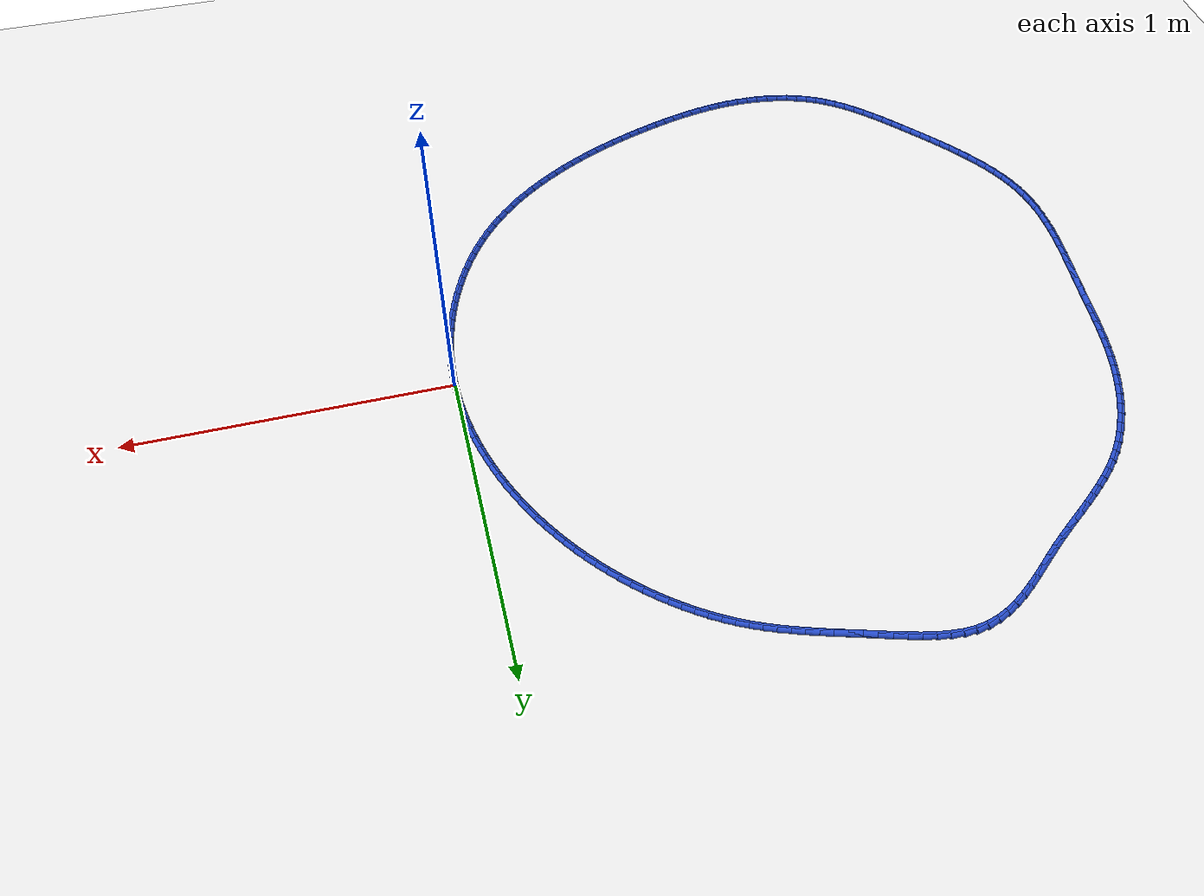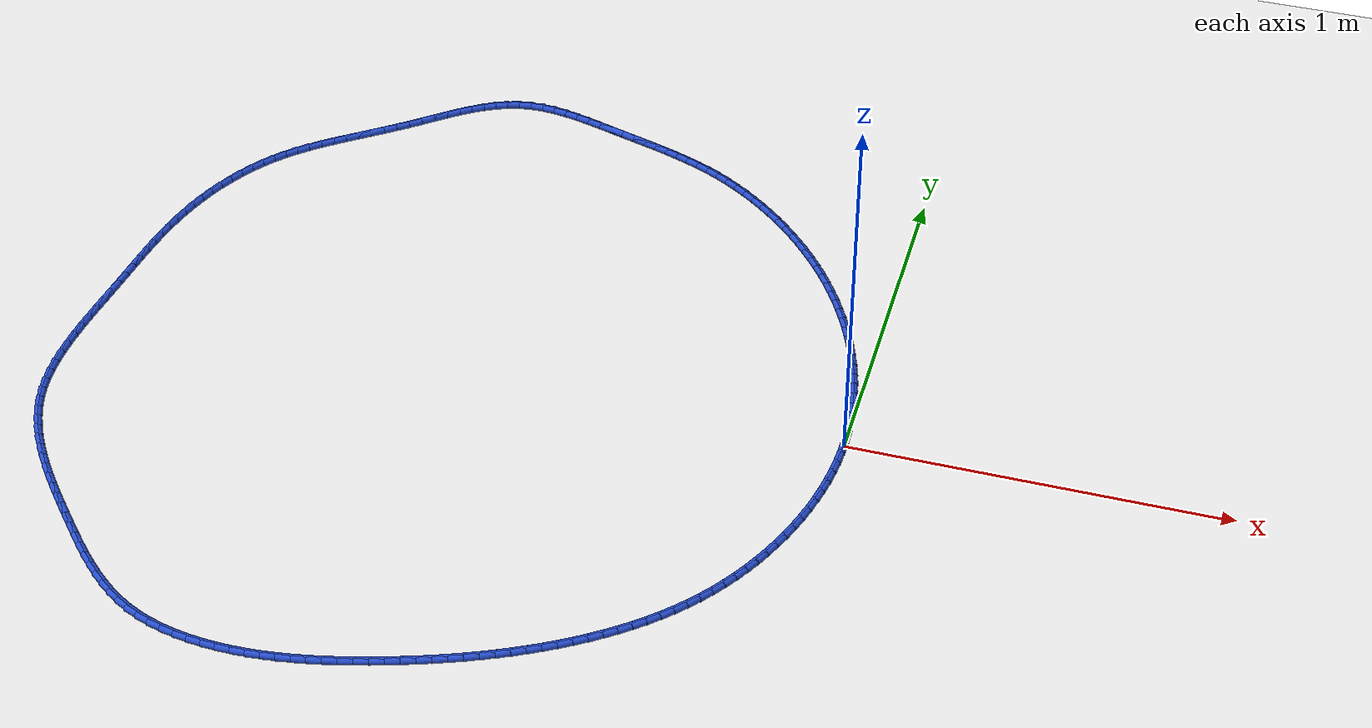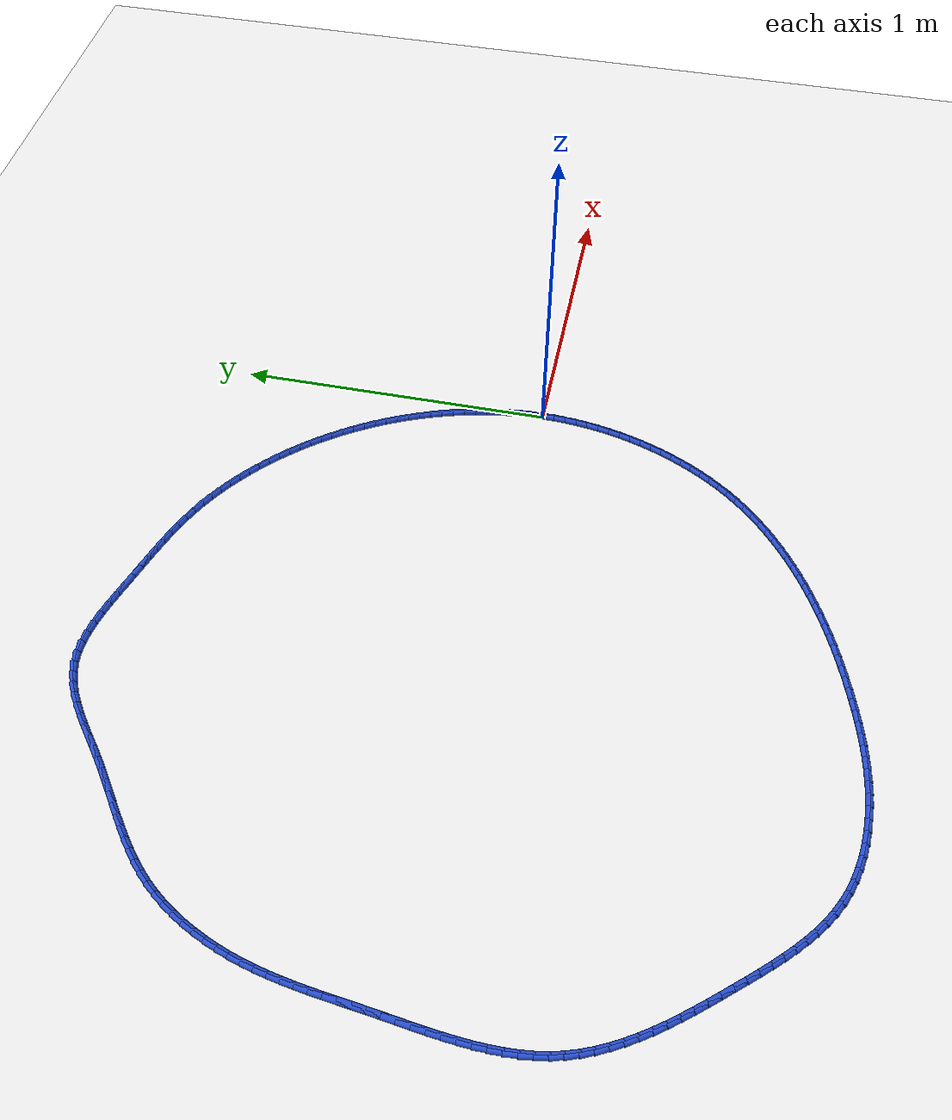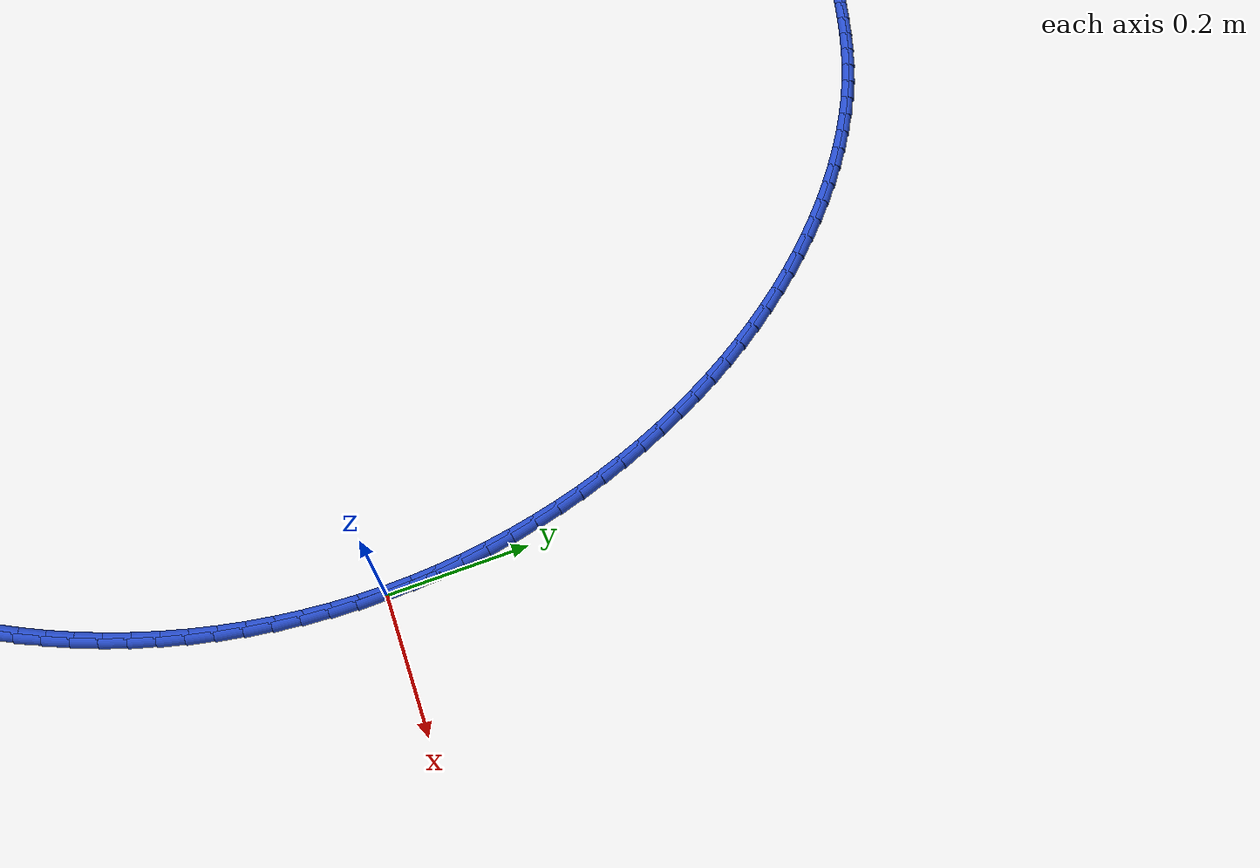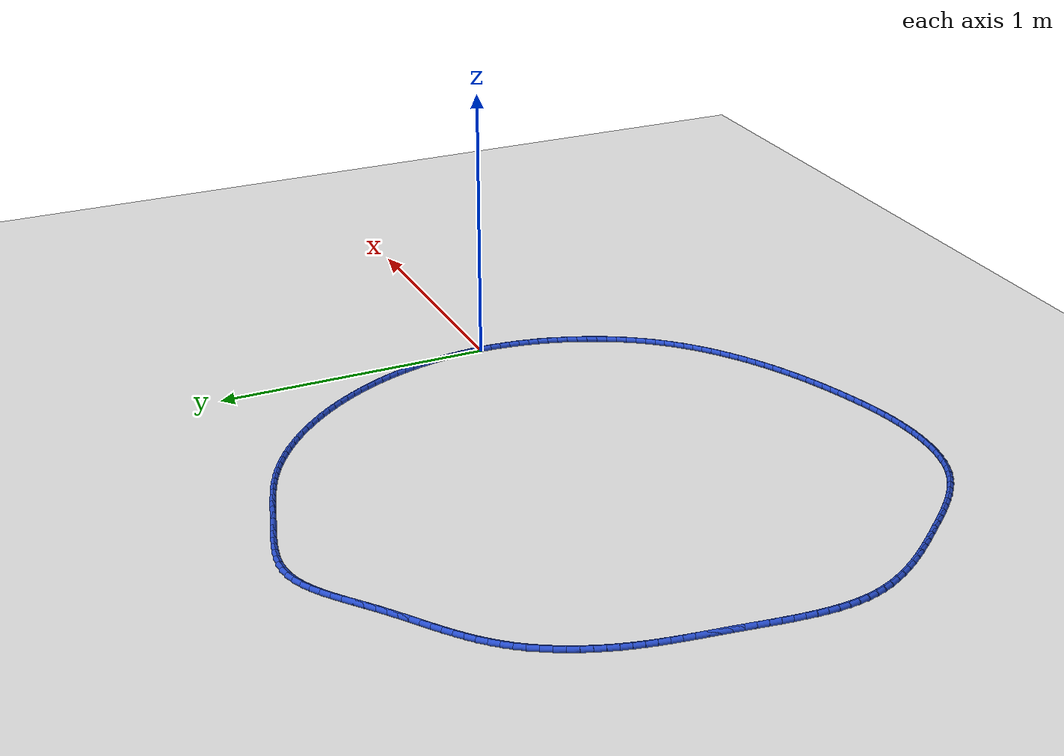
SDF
<sdf version="1.6">
 <world name="default">
  <light name="sun" type="directional">
   <pose>0 0 10 0 -0 0</pose>
   <diffuse>0.8 0.8 0.8 1</diffuse>
   <specular>0.2 0.2 0.2 1</specular>
   <attenuation>
    <range>1000</range>
    <constant>0.9</constant>
    <linear>0.01</linear>
    <quadratic>0.001</quadratic>
   </attenuation>
   <direction>-0.5 0.1 -0.9</direction>
  </light>
  <model name="ground_plane">
   <static>1</static>
   <link name="link">
    <collision name="collision">
     <geometry><plane><normal>0 0 1</normal><size>100 100</size></plane></geometry>
     <surface><friction><ode><mu>100</mu><mu2>50</mu2></ode></friction></surface>
    </collision>
    <visual name="visual">
     <cast_shadows>0</cast_shadows>
     <geometry><plane><normal>0 0 1</normal><size>100 100</size></plane></geometry>
     <material>
      <script><uri>file://media/materials/scripts/gazebo.material</uri><name>Gazebo/WhiteGlow</name></script>
     </material>
    </visual>
   </link>
  </model>
  <gravity>0 0 -9.8</gravity>
  <magnetic_field>6e-06 2.3e-05 -4.2e-05</magnetic_field>
  <atmosphere type="adiabatic"/>
  <physics name="default_physics" default="0" type="ode">
   <max_step_size>0.001</max_step_size>
   <real_time_factor>1</real_time_factor>
   <real_time_update_rate>1000</real_time_update_rate>
  </physics>
  <scene><ambient>0.4 0.4 0.4 1</ambient><background>0.7 0.7 0.7 1</background><shadows>1</shadows></scene>
  <spherical_coordinates>
   <surface_model>EARTH_WGS84</surface_model>
   <latitude_deg>0</latitude_deg>
   <longitude_deg>0</longitude_deg>
   <elevation>0</elevation>
   <heading_deg>0</heading_deg>
  </spherical_coordinates>
  <model name="line">
   <link name="link_0">
    <pose>1.734723475976807e-18 6.938893903907228e-18 0.01 0 1.57 -1.548803812071096</pose>
    <collision name="collision">
     <geometry><cylinder><radius>0.01</radius><length>0.08</length></cylinder></geometry>
    </collision>
    <visual name="visual">
     <material>
      <script><name>Gazebo/Blue</name><uri>file://media/materials/scripts/gazebo.material</uri></script>
     </material>
     <geometry><cylinder><radius>0.01</radius><length>0.08</length></cylinder></geometry>
    </visual>
   </link>
   <link name="link_1">
    <pose>-0.0008166172128536515 0.0371256111873309 0.01 0 1.57 -1.5104553792389328</pose>
    <collision name="collision">
     <geometry><cylinder><radius>0.01</radius><length>0.08</length></cylinder></geometry>
    </collision>
    <visual name="visual">
     <material>
      <script><name>Gazebo/Blue</name><uri>file://media/materials/scripts/gazebo.material</uri></script>
     </material>
     <geometry><cylinder><radius>0.01</radius><length>0.08</length></cylinder></geometry>
    </visual>
   </link>
   <link name="link_2">
    <pose>-0.003056414222960652 0.07419957259008825 0.01 0 1.57 -1.4729570033766226</pose>
    <collision name="collision">
     <geometry><cylinder><radius>0.01</radius><length>0.08</length></cylinder></geometry>
    </collision>
    <visual name="visual">
     <material>
      <script><name>Gazebo/Blue</name><uri>file://media/materials/scripts/gazebo.material</uri></script>
     </material>
     <geometry><cylinder><radius>0.01</radius><length>0.08</length></cylinder></geometry>
    </visual>
   </link>
   <link name="link_3">
    <pose>-0.006686239691049554 0.11118097981215619 0.01 0 1.57 -1.4362816621876346</pose>
    <collision name="collision">
     <geometry><cylinder><radius>0.01</radius><length>0.08</length></cylinder></geometry>
    </collision>
    <visual name="visual">
     <material>
      <script><name>Gazebo/Blue</name><uri>file://media/materials/scripts/gazebo.material</uri></script>
     </material>
     <geometry><cylinder><radius>0.01</radius><length>0.08</length></cylinder></geometry>
    </visual>
   </link>
   <link name="link_4">
    <pose>-0.011672942277848868 0.14802892845741888 0.01 0 1.57 -1.4003948842519711</pose>
    <collision name="collision">
     <geometry><cylinder><radius>0.01</radius><length>0.08</length></cylinder></geometry>
    </collision>
    <visual name="visual">
     <material>
      <script><name>Gazebo/Blue</name><uri>file://media/materials/scripts/gazebo.material</uri></script>
     </material>
     <geometry><cylinder><radius>0.01</radius><length>0.08</length></cylinder></geometry>
    </visual>
   </link>
   <link name="link_5">
    <pose>-0.01798337064408713 0.18470251412976016 0.01 0 1.57 -1.365255838852558</pose>
    <collision name="collision">
     <geometry><cylinder><radius>0.01</radius><length>0.08</length></cylinder></geometry>
    </collision>
    <visual name="visual">
     <material>
      <script><name>Gazebo/Blue</name><uri>file://media/materials/scripts/gazebo.material</uri></script>
     </material>
     <geometry><cylinder><radius>0.01</radius><length>0.08</length></cylinder></geometry>
    </visual>
   </link>
   <link name="link_6">
    <pose>-0.025584373450492873 0.22116083243306434 0.01 0 1.57 -1.3308183238178624</pose>
    <collision name="collision">
     <geometry><cylinder><radius>0.01</radius><length>0.08</length></cylinder></geometry>
    </collision>
    <visual name="visual">
     <material>
      <script><name>Gazebo/Blue</name><uri>file://media/materials/scripts/gazebo.material</uri></script>
     </material>
     <geometry><cylinder><radius>0.01</radius><length>0.08</length></cylinder></geometry>
    </visual>
   </link>
   <link name="link_7">
    <pose>-0.03444279935779465 0.2573629789712155 0.01 0 1.57 -1.2970316387056642</pose>
    <collision name="collision">
     <geometry><cylinder><radius>0.01</radius><length>0.08</length></cylinder></geometry>
    </collision>
    <visual name="visual">
     <material>
      <script><name>Gazebo/Blue</name><uri>file://media/materials/scripts/gazebo.material</uri></script>
     </material>
     <geometry><cylinder><radius>0.01</radius><length>0.08</length></cylinder></geometry>
    </visual>
   </link>
   <link name="link_8">
    <pose>-0.04452549702672097 0.2932680493480976 0.01 0 1.57 -1.2638413381549296</pose>
    <collision name="collision">
     <geometry><cylinder><radius>0.01</radius><length>0.08</length></cylinder></geometry>
    </collision>
    <visual name="visual">
     <material>
      <script><name>Gazebo/Blue</name><uri>file://media/materials/scripts/gazebo.material</uri></script>
     </material>
     <geometry><cylinder><radius>0.01</radius><length>0.08</length></cylinder></geometry>
    </visual>
   </link>
   <link name="link_9">
    <pose>-0.05579931511800036 0.32883513916759466 0.01 0 1.57 -1.2311793892716603</pose>
    <collision name="collision">
     <geometry><cylinder><radius>0.01</radius><length>0.08</length></cylinder></geometry>
    </collision>
    <visual name="visual">
     <material>
      <script><name>Gazebo/Blue</name><uri>file://media/materials/scripts/gazebo.material</uri></script>
     </material>
     <geometry><cylinder><radius>0.01</radius><length>0.08</length></cylinder></geometry>
    </visual>
   </link>
   <link name="link_10">
    <pose>-0.06823165247662019 0.36402372758744195 0.01 0 1.57 -1.1988521572908928</pose>
    <collision name="collision">
     <geometry><cylinder><radius>0.01</radius><length>0.08</length></cylinder></geometry>
    </collision>
    <visual name="visual">
     <material>
      <script><name>Gazebo/Blue</name><uri>file://media/materials/scripts/gazebo.material</uri></script>
     </material>
     <geometry><cylinder><radius>0.01</radius><length>0.08</length></cylinder></geometry>
    </visual>
   </link>
   <link name="link_11">
    <pose>-0.08179733110301537 0.39879846872233216 0.01 0 1.57 -1.1667260969815054</pose>
    <collision name="collision">
     <geometry><cylinder><radius>0.01</radius><length>0.08</length></cylinder></geometry>
    </collision>
    <visual name="visual">
     <material>
      <script><name>Gazebo/Blue</name><uri>file://media/materials/scripts/gazebo.material</uri></script>
     </material>
     <geometry><cylinder><radius>0.01</radius><length>0.08</length></cylinder></geometry>
    </visual>
   </link>
   <link name="link_12">
    <pose>-0.09647649984277216 0.4331277302282644 0.01 0 1.57 -1.1347705208000163</pose>
    <collision name="collision">
     <geometry><cylinder><radius>0.01</radius><length>0.08</length></cylinder></geometry>
    </collision>
    <visual name="visual">
     <material>
      <script><name>Gazebo/Blue</name><uri>file://media/materials/scripts/gazebo.material</uri></script>
     </material>
     <geometry><cylinder><radius>0.01</radius><length>0.08</length></cylinder></geometry>
    </visual>
   </link>
   <link name="link_13">
    <pose>-0.11224942393682984 0.46697996090475546 0.01 0 1.57 -1.1029559619684848</pose>
    <collision name="collision">
     <geometry><cylinder><radius>0.01</radius><length>0.08</length></cylinder></geometry>
    </collision>
    <visual name="visual">
     <material>
      <script><name>Gazebo/Blue</name><uri>file://media/materials/scripts/gazebo.material</uri></script>
     </material>
     <geometry><cylinder><radius>0.01</radius><length>0.08</length></cylinder></geometry>
    </visual>
   </link>
   <link name="link_14">
    <pose>-0.12909636862612736 0.5003236095513213 0.01 0 1.57 -1.0712521805309185</pose>
    <collision name="collision">
     <geometry><cylinder><radius>0.01</radius><length>0.08</length></cylinder></geometry>
    </collision>
    <visual name="visual">
     <material>
      <script><name>Gazebo/Blue</name><uri>file://media/materials/scripts/gazebo.material</uri></script>
     </material>
     <geometry><cylinder><radius>0.01</radius><length>0.08</length></cylinder></geometry>
    </visual>
   </link>
   <link name="link_15">
    <pose>-0.14699759915160396 0.5331271249674784 0.01 0 1.57 -1.0396283739457042</pose>
    <collision name="collision">
     <geometry><cylinder><radius>0.01</radius><length>0.08</length></cylinder></geometry>
    </collision>
    <visual name="visual">
     <material>
      <script><name>Gazebo/Blue</name><uri>file://media/materials/scripts/gazebo.material</uri></script>
     </material>
     <geometry><cylinder><radius>0.01</radius><length>0.08</length></cylinder></geometry>
    </visual>
   </link>
   <link name="link_16">
    <pose>-0.16593338075419867 0.5653589559527432 0.01 0 1.57 -1.0080533781159469</pose>
    <collision name="collision">
     <geometry><cylinder><radius>0.01</radius><length>0.08</length></cylinder></geometry>
    </collision>
    <visual name="visual">
     <material>
      <script><name>Gazebo/Blue</name><uri>file://media/materials/scripts/gazebo.material</uri></script>
     </material>
     <geometry><cylinder><radius>0.01</radius><length>0.08</length></cylinder></geometry>
    </visual>
   </link>
   <link name="link_17">
    <pose>-0.18588397867485068 0.5969875513066321 0.01 0 1.57 -0.9764958613945641</pose>
    <collision name="collision">
     <geometry><cylinder><radius>0.01</radius><length>0.08</length></cylinder></geometry>
    </collision>
    <visual name="visual">
     <material>
      <script><name>Gazebo/Blue</name><uri>file://media/materials/scripts/gazebo.material</uri></script>
     </material>
     <geometry><cylinder><radius>0.01</radius><length>0.08</length></cylinder></geometry>
    </visual>
   </link>
   <link name="link_18">
    <pose>-0.20682965815449908 0.6279813598286613 0.01 0 1.57 -0.9449245142598489</pose>
    <collision name="collision">
     <geometry><cylinder><radius>0.01</radius><length>0.08</length></cylinder></geometry>
    </collision>
    <visual name="visual">
     <material>
      <script><name>Gazebo/Blue</name><uri>file://media/materials/scripts/gazebo.material</uri></script>
     </material>
     <geometry><cylinder><radius>0.01</radius><length>0.08</length></cylinder></geometry>
    </visual>
   </link>
   <link name="link_19">
    <pose>-0.22875068443408303 0.6583088303183473 0.01 0 1.57 -0.9133082374298498</pose>
    <collision name="collision">
     <geometry><cylinder><radius>0.01</radius><length>0.08</length></cylinder></geometry>
    </collision>
    <visual name="visual">
     <material>
      <script><name>Gazebo/Blue</name><uri>file://media/materials/scripts/gazebo.material</uri></script>
     </material>
     <geometry><cylinder><radius>0.01</radius><length>0.08</length></cylinder></geometry>
    </visual>
   </link>
   <link name="link_20">
    <pose>-0.2516273227545417 0.6879384115752066 0.01 0 1.57 -0.8816163311751766</pose>
    <collision name="collision">
     <geometry><cylinder><radius>0.01</radius><length>0.08</length></cylinder></geometry>
    </collision>
    <visual name="visual">
     <material>
      <script><name>Gazebo/Blue</name><uri>file://media/materials/scripts/gazebo.material</uri></script>
     </material>
     <geometry><cylinder><radius>0.01</radius><length>0.08</length></cylinder></geometry>
    </visual>
   </link>
   <link name="link_21">
    <pose>-0.27543983835681407 0.7168385523987553 0.01 0 1.57 -0.8498186885022461</pose>
    <collision name="collision">
     <geometry><cylinder><radius>0.01</radius><length>0.08</length></cylinder></geometry>
    </collision>
    <visual name="visual">
     <material>
      <script><name>Gazebo/Blue</name><uri>file://media/materials/scripts/gazebo.material</uri></script>
     </material>
     <geometry><cylinder><radius>0.01</radius><length>0.08</length></cylinder></geometry>
    </visual>
   </link>
   <link name="link_22">
    <pose>-0.3001684964818394 0.7449777015885098 0.01 0 1.57 -0.8178859947104978</pose>
    <collision name="collision">
     <geometry><cylinder><radius>0.01</radius><length>0.08</length></cylinder></geometry>
    </collision>
    <visual name="visual">
     <material>
      <script><name>Gazebo/Blue</name><uri>file://media/materials/scripts/gazebo.material</uri></script>
     </material>
     <geometry><cylinder><radius>0.01</radius><length>0.08</length></cylinder></geometry>
    </visual>
   </link>
   <link name="link_23">
    <pose>-0.32579356237055673 0.7723243079439869 0.01 0 1.57 -0.7857899355739253</pose>
    <collision name="collision">
     <geometry><cylinder><radius>0.01</radius><length>0.08</length></cylinder></geometry>
    </collision>
    <visual name="visual">
     <material>
      <script><name>Gazebo/Blue</name><uri>file://media/materials/scripts/gazebo.material</uri></script>
     </material>
     <geometry><cylinder><radius>0.01</radius><length>0.08</length></cylinder></geometry>
    </visual>
   </link>
   <link name="link_24">
    <pose>-0.35229530126390507 0.7988468202647022 0.01 0 1.57 -0.7534852242860435</pose>
    <collision name="collision">
     <geometry><cylinder><radius>0.01</radius><length>0.08</length></cylinder></geometry>
    </collision>
    <visual name="visual">
     <material>
      <script><name>Gazebo/Blue</name><uri>file://media/materials/scripts/gazebo.material</uri></script>
     </material>
     <geometry><cylinder><radius>0.01</radius><length>0.08</length></cylinder></geometry>
    </visual>
   </link>
   <link name="link_25">
    <pose>-0.379653244259535 0.8245120628915645 0.01 0 1.57 -0.7206457512692492</pose>
    <collision name="collision">
     <geometry><cylinder><radius>0.01</radius><length>0.08</length></cylinder></geometry>
    </collision>
    <visual name="visual">
     <material>
      <script><name>Gazebo/Blue</name><uri>file://media/materials/scripts/gazebo.material</uri></script>
     </material>
     <geometry><cylinder><radius>0.01</radius><length>0.08</length></cylinder></geometry>
    </visual>
   </link>
   <link name="link_26">
    <pose>-0.4078358339566967 0.8492623243467254 0.01 0 1.57 -0.6869321946132785</pose>
    <collision name="collision">
     <geometry><cylinder><radius>0.01</radius><length>0.08</length></cylinder></geometry>
    </collision>
    <visual name="visual">
     <material>
      <script><name>Gazebo/Blue</name><uri>file://media/materials/scripts/gazebo.material</uri></script>
     </material>
     <geometry><cylinder><radius>0.01</radius><length>0.08</length></cylinder></geometry>
    </visual>
   </link>
   <link name="link_27">
    <pose>-0.43680292373964574 0.8730208875652158 0.01 0 1.57 -0.6521944734723227</pose>
    <collision name="collision">
     <geometry><cylinder><radius>0.01</radius><length>0.08</length></cylinder></geometry>
    </collision>
    <visual name="visual">
     <material>
      <script><name>Gazebo/Blue</name><uri>file://media/materials/scripts/gazebo.material</uri></script>
     </material>
     <geometry><cylinder><radius>0.01</radius><length>0.08</length></cylinder></geometry>
    </visual>
   </link>
   <link name="link_28">
    <pose>-0.46651414294938937 0.8957105397355428 0.01 0 1.57 -0.616287864081767</pose>
    <collision name="collision">
     <geometry><cylinder><radius>0.01</radius><length>0.08</length></cylinder></geometry>
    </collision>
    <visual name="visual">
     <material>
      <script><name>Gazebo/Blue</name><uri>file://media/materials/scripts/gazebo.material</uri></script>
     </material>
     <geometry><cylinder><radius>0.01</radius><length>0.08</length></cylinder></geometry>
    </visual>
   </link>
   <link name="link_29">
    <pose>-0.49692912092693453 0.9172540680462133 0.01 0 1.57 -0.5790679919848344</pose>
    <collision name="collision">
     <geometry><cylinder><radius>0.01</radius><length>0.08</length></cylinder></geometry>
    </collision>
    <visual name="visual">
     <material>
      <script><name>Gazebo/Blue</name><uri>file://media/materials/scripts/gazebo.material</uri></script>
     </material>
     <geometry><cylinder><radius>0.01</radius><length>0.08</length></cylinder></geometry>
    </visual>
   </link>
   <link name="link_30">
    <pose>-0.5280074870132879 0.937574259685733 0.01 0 1.57 -0.5403919457006781</pose>
    <collision name="collision">
     <geometry><cylinder><radius>0.01</radius><length>0.08</length></cylinder></geometry>
    </collision>
    <visual name="visual">
     <material>
      <script><name>Gazebo/Blue</name><uri>file://media/materials/scripts/gazebo.material</uri></script>
     </material>
     <geometry><cylinder><radius>0.01</radius><length>0.08</length></cylinder></geometry>
    </visual>
   </link>
   <link name="link_31">
    <pose>-0.5597088705494562 0.9565939018426093 0.01 0 1.57 -0.5001200737778002</pose>
    <collision name="collision">
     <geometry><cylinder><radius>0.01</radius><length>0.08</length></cylinder></geometry>
    </collision>
    <visual name="visual">
     <material>
      <script><name>Gazebo/Blue</name><uri>file://media/materials/scripts/gazebo.material</uri></script>
     </material>
     <geometry><cylinder><radius>0.01</radius><length>0.08</length></cylinder></geometry>
    </visual>
   </link>
   <link name="link_32">
    <pose>-0.5919929008764467 0.9742357817053481 0.01 0 1.57 -0.4581635751073741</pose>
    <collision name="collision">
     <geometry><cylinder><radius>0.01</radius><length>0.08</length></cylinder></geometry>
    </collision>
    <visual name="visual">
     <material>
      <script><name>Gazebo/Blue</name><uri>file://media/materials/scripts/gazebo.material</uri></script>
     </material>
     <geometry><cylinder><radius>0.01</radius><length>0.08</length></cylinder></geometry>
    </visual>
   </link>
   <link name="link_33">
    <pose>-0.6248193930607605 0.990424613899813 0.01 0 1.57 -0.4170047854627513</pose>
    <collision name="collision">
     <geometry><cylinder><radius>0.01</radius><length>0.08</length></cylinder></geometry>
    </collision>
    <visual name="visual">
     <material>
      <script><name>Gazebo/Blue</name><uri>file://media/materials/scripts/gazebo.material</uri></script>
     </material>
     <geometry><cylinder><radius>0.01</radius><length>0.08</length></cylinder></geometry>
    </visual>
   </link>
   <link name="link_34">
    <pose>-0.6581585939559912 1.0051933729125293 0.01 0 1.57 -0.38076561511235363</pose>
    <collision name="collision">
     <geometry><cylinder><radius>0.01</radius><length>0.08</length></cylinder></geometry>
    </collision>
    <visual name="visual">
     <material>
      <script><name>Gazebo/Blue</name><uri>file://media/materials/scripts/gazebo.material</uri></script>
     </material>
     <geometry><cylinder><radius>0.01</radius><length>0.08</length></cylinder></geometry>
    </visual>
   </link>
   <link name="link_35">
    <pose>-0.6919965231943169 1.0187387212727943 0.01 0 1.57 -0.3500765276781353</pose>
    <collision name="collision">
     <geometry><cylinder><radius>0.01</radius><length>0.08</length></cylinder></geometry>
    </collision>
    <visual name="visual">
     <material>
      <script><name>Gazebo/Blue</name><uri>file://media/materials/scripts/gazebo.material</uri></script>
     </material>
     <geometry><cylinder><radius>0.01</radius><length>0.08</length></cylinder></geometry>
    </visual>
   </link>
   <link name="link_36">
    <pose>-0.7263205119005703 1.0312709320265703 0.01 0 1.57 -0.32511477084612067</pose>
    <collision name="collision">
     <geometry><cylinder><radius>0.01</radius><length>0.08</length></cylinder></geometry>
    </collision>
    <visual name="visual">
     <material>
      <script><name>Gazebo/Blue</name><uri>file://media/materials/scripts/gazebo.material</uri></script>
     </material>
     <geometry><cylinder><radius>0.01</radius><length>0.08</length></cylinder></geometry>
    </visual>
   </link>
   <link name="link_37">
    <pose>-0.7611178911995843 1.0430002782198204 0.01 0 1.57 -0.3059463766919465</pose>
    <collision name="collision">
     <geometry><cylinder><radius>0.01</radius><length>0.08</length></cylinder></geometry>
    </collision>
    <visual name="visual">
     <material>
      <script><name>Gazebo/Blue</name><uri>file://media/materials/scripts/gazebo.material</uri></script>
     </material>
     <geometry><cylinder><radius>0.01</radius><length>0.08</length></cylinder></geometry>
    </visual>
   </link>
   <link name="link_38">
    <pose>-0.7963759922161912 1.0541370328985071 0.01 0 1.57 -0.2925507404638758</pose>
    <collision name="collision">
     <geometry><cylinder><radius>0.01</radius><length>0.08</length></cylinder></geometry>
    </collision>
    <visual name="visual">
     <material>
      <script><name>Gazebo/Blue</name><uri>file://media/materials/scripts/gazebo.material</uri></script>
     </material>
     <geometry><cylinder><radius>0.01</radius><length>0.08</length></cylinder></geometry>
    </visual>
   </link>
   <link name="link_39">
    <pose>-0.8320821460752243 1.0648914691085936 0.01 0 1.57 -0.284842055436603</pose>
    <collision name="collision">
     <geometry><cylinder><radius>0.01</radius><length>0.08</length></cylinder></geometry>
    </collision>
    <visual name="visual">
     <material>
      <script><name>Gazebo/Blue</name><uri>file://media/materials/scripts/gazebo.material</uri></script>
     </material>
     <geometry><cylinder><radius>0.01</radius><length>0.08</length></cylinder></geometry>
    </visual>
   </link>
   <link name="link_40">
    <pose>-0.8682236839015163 1.0754738598960423 0.01 0 1.57 -0.28268585916986205</pose>
    <collision name="collision">
     <geometry><cylinder><radius>0.01</radius><length>0.08</length></cylinder></geometry>
    </collision>
    <visual name="visual">
     <material>
      <script><name>Gazebo/Blue</name><uri>file://media/materials/scripts/gazebo.material</uri></script>
     </material>
     <geometry><cylinder><radius>0.01</radius><length>0.08</length></cylinder></geometry>
    </visual>
   </link>
   <link name="link_41">
    <pose>-0.9047879368198998 1.0860944783068163 0.01 0 1.57 -0.28570169210642626</pose>
    <collision name="collision">
     <geometry><cylinder><radius>0.01</radius><length>0.08</length></cylinder></geometry>
    </collision>
    <visual name="visual">
     <material>
      <script><name>Gazebo/Blue</name><uri>file://media/materials/scripts/gazebo.material</uri></script>
     </material>
     <geometry><cylinder><radius>0.01</radius><length>0.08</length></cylinder></geometry>
    </visual>
   </link>
   <link name="link_42">
    <pose>-0.9417604463109354 1.0969546975188447 0.01 0 1.57 -0.28590806677265207</pose>
    <collision name="collision">
     <geometry><cylinder><radius>0.01</radius><length>0.08</length></cylinder></geometry>
    </collision>
    <visual name="visual">
     <material>
      <script><name>Gazebo/Blue</name><uri>file://media/materials/scripts/gazebo.material</uri></script>
     </material>
     <geometry><cylinder><radius>0.01</radius><length>0.08</length></cylinder></geometry>
    </visual>
   </link>
   <link name="link_43">
    <pose>-0.9790590210083654 1.1079190565092116 0.01 0 1.57 -0.27333436072070205</pose>
    <collision name="collision">
     <geometry><cylinder><radius>0.01</radius><length>0.08</length></cylinder></geometry>
    </collision>
    <visual name="visual">
     <material>
      <script><name>Gazebo/Blue</name><uri>file://media/materials/scripts/gazebo.material</uri></script>
     </material>
     <geometry><cylinder><radius>0.01</radius><length>0.08</length></cylinder></geometry>
    </visual>
   </link>
   <link name="link_44">
    <pose>-1.0165145318548088 1.1184197547168324 0.01 0 1.57 -0.24702548095925173</pose>
    <collision name="collision">
     <geometry><cylinder><radius>0.01</radius><length>0.08</length></cylinder></geometry>
    </collision>
    <visual name="visual">
     <material>
      <script><name>Gazebo/Blue</name><uri>file://media/materials/scripts/gazebo.material</uri></script>
     </material>
     <geometry><cylinder><radius>0.01</radius><length>0.08</length></cylinder></geometry>
    </visual>
   </link>
   <link name="link_45">
    <pose>-1.0539521439984387 1.1278606167698348 0.01 0 1.57 -0.2060514984577185</pose>
    <collision name="collision">
     <geometry><cylinder><radius>0.01</radius><length>0.08</length></cylinder></geometry>
    </collision>
    <visual name="visual">
     <material>
      <script><name>Gazebo/Blue</name><uri>file://media/materials/scripts/gazebo.material</uri></script>
     </material>
     <geometry><cylinder><radius>0.01</radius><length>0.08</length></cylinder></geometry>
    </visual>
   </link>
   <link name="link_46">
    <pose>-1.0911970225874292 1.1356454672963472 0.01 0 1.57 -0.1489182472577403</pose>
    <collision name="collision">
     <geometry><cylinder><radius>0.01</radius><length>0.08</length></cylinder></geometry>
    </collision>
    <visual name="visual">
     <material>
      <script><name>Gazebo/Blue</name><uri>file://media/materials/scripts/gazebo.material</uri></script>
     </material>
     <geometry><cylinder><radius>0.01</radius><length>0.08</length></cylinder></geometry>
    </visual>
   </link>
   <link name="link_47">
    <pose>-1.1280743327699527 1.1411781309244975 0.01 0 1.57 -0.07374269235701547</pose>
    <collision name="collision">
     <geometry><cylinder><radius>0.01</radius><length>0.08</length></cylinder></geometry>
    </collision>
    <visual name="visual">
     <material>
      <script><name>Gazebo/Blue</name><uri>file://media/materials/scripts/gazebo.material</uri></script>
     </material>
     <geometry><cylinder><radius>0.01</radius><length>0.08</length></cylinder></geometry>
    </visual>
   </link>
   <link name="link_48">
    <pose>-1.1644092396941828 1.1438624322824136 0.01 0 1.57 0.021341117797742396</pose>
    <collision name="collision">
     <geometry><cylinder><radius>0.01</radius><length>0.08</length></cylinder></geometry>
    </collision>
    <visual name="visual">
     <material>
      <script><name>Gazebo/Blue</name><uri>file://media/materials/scripts/gazebo.material</uri></script>
     </material>
     <geometry><cylinder><radius>0.01</radius><length>0.08</length></cylinder></geometry>
    </visual>
   </link>
   <link name="link_49">
    <pose>-1.2000269085082929 1.1431021959982233 0.01 0 1.57 0.13738300438065437</pose>
    <collision name="collision">
     <geometry><cylinder><radius>0.01</radius><length>0.08</length></cylinder></geometry>
    </collision>
    <visual name="visual">
     <material>
      <script><name>Gazebo/Blue</name><uri>file://media/materials/scripts/gazebo.material</uri></script>
     </material>
     <geometry><cylinder><radius>0.01</radius><length>0.08</length></cylinder></geometry>
    </visual>
   </link>
   <link name="link_50">
    <pose>-1.2347525043658543 1.1383012467203608 0.01 0 1.57 0.2673403412451808</pose>
    <collision name="collision">
     <geometry><cylinder><radius>0.01</radius><length>0.08</length></cylinder></geometry>
    </collision>
    <visual name="visual">
     <material>
      <script><name>Gazebo/Blue</name><uri>file://media/materials/scripts/gazebo.material</uri></script>
     </material>
     <geometry><cylinder><radius>0.01</radius><length>0.08</length></cylinder></geometry>
    </visual>
   </link>
   <link name="link_51">
    <pose>-1.2684654268030346 1.1290673831311249 0.01 0 1.57 0.3841018119666909</pose>
    <collision name="collision">
     <geometry><cylinder><radius>0.01</radius><length>0.08</length></cylinder></geometry>
    </collision>
    <visual name="visual">
     <material>
      <script><name>Gazebo/Blue</name><uri>file://media/materials/scripts/gazebo.material</uri></script>
     </material>
     <geometry><cylinder><radius>0.01</radius><length>0.08</length></cylinder></geometry>
    </visual>
   </link>
   <link name="link_52">
    <pose>-1.301259003675692 1.1158129824889484 0.01 0 1.57 0.47985480022445526</pose>
    <collision name="collision">
     <geometry><cylinder><radius>0.01</radius><length>0.08</length></cylinder></geometry>
    </collision>
    <visual name="visual">
     <material>
      <script><name>Gazebo/Blue</name><uri>file://media/materials/scripts/gazebo.material</uri></script>
     </material>
     <geometry><cylinder><radius>0.01</radius><length>0.08</length></cylinder></geometry>
    </visual>
   </link>
   <link name="link_53">
    <pose>-1.333279303023399 1.0991487764448922 0.01 0 1.57 0.5549856970457381</pose>
    <collision name="collision">
     <geometry><cylinder><radius>0.01</radius><length>0.08</length></cylinder></geometry>
    </collision>
    <visual name="visual">
     <material>
      <script><name>Gazebo/Blue</name><uri>file://media/materials/scripts/gazebo.material</uri></script>
     </material>
     <geometry><cylinder><radius>0.01</radius><length>0.08</length></cylinder></geometry>
    </visual>
   </link>
   <link name="link_54">
    <pose>-1.3646723928857292 1.0796854966500178 0.01 0 1.57 0.6110137558843318</pose>
    <collision name="collision">
     <geometry><cylinder><radius>0.01</radius><length>0.08</length></cylinder></geometry>
    </collision>
    <visual name="visual">
     <material>
      <script><name>Gazebo/Blue</name><uri>file://media/materials/scripts/gazebo.material</uri></script>
     </material>
     <geometry><cylinder><radius>0.01</radius><length>0.08</length></cylinder></geometry>
    </visual>
   </link>
   <link name="link_55">
    <pose>-1.3955843413022553 1.0580338747553857 0.01 0 1.57 0.6496798531786511</pose>
    <collision name="collision">
     <geometry><cylinder><radius>0.01</radius><length>0.08</length></cylinder></geometry>
    </collision>
    <visual name="visual">
     <material>
      <script><name>Gazebo/Blue</name><uri>file://media/materials/scripts/gazebo.material</uri></script>
     </material>
     <geometry><cylinder><radius>0.01</radius><length>0.08</length></cylinder></geometry>
    </visual>
   </link>
   <link name="link_56">
    <pose>-1.4261612163125503 1.0348046424120578 0.01 0 1.57 0.6724455371051267</pose>
    <collision name="collision">
     <geometry><cylinder><radius>0.01</radius><length>0.08</length></cylinder></geometry>
    </collision>
    <visual name="visual">
     <material>
      <script><name>Gazebo/Blue</name><uri>file://media/materials/scripts/gazebo.material</uri></script>
     </material>
     <geometry><cylinder><radius>0.01</radius><length>0.08</length></cylinder></geometry>
    </visual>
   </link>
   <link name="link_57">
    <pose>-1.4565490859561874 1.0106085312710953 0.01 0 1.57 0.6802686006759554</pose>
    <collision name="collision">
     <geometry><cylinder><radius>0.01</radius><length>0.08</length></cylinder></geometry>
    </collision>
    <visual name="visual">
     <material>
      <script><name>Gazebo/Blue</name><uri>file://media/materials/scripts/gazebo.material</uri></script>
     </material>
     <geometry><cylinder><radius>0.01</radius><length>0.08</length></cylinder></geometry>
    </visual>
   </link>
   <link name="link_58">
    <pose>-1.4868940182727397 0.9860562729835587 0.01 0 1.57 0.673522637209146</pose>
    <collision name="collision">
     <geometry><cylinder><radius>0.01</radius><length>0.08</length></cylinder></geometry>
    </collision>
    <visual name="visual">
     <material>
      <script><name>Gazebo/Blue</name><uri>file://media/materials/scripts/gazebo.material</uri></script>
     </material>
     <geometry><cylinder><radius>0.01</radius><length>0.08</length></cylinder></geometry>
    </visual>
   </link>
   <link name="link_59">
    <pose>-1.51734208130178 0.96175859920051 0.01 0 1.57 0.6540397710297732</pose>
    <collision name="collision">
     <geometry><cylinder><radius>0.01</radius><length>0.08</length></cylinder></geometry>
    </collision>
    <visual name="visual">
     <material>
      <script><name>Gazebo/Blue</name><uri>file://media/materials/scripts/gazebo.material</uri></script>
     </material>
     <geometry><cylinder><radius>0.01</radius><length>0.08</length></cylinder></geometry>
    </visual>
   </link>
   <link name="link_60">
    <pose>-1.5480107119347557 0.9382480739268022 0.01 0 1.57 0.635792416085352</pose>
    <collision name="collision">
     <geometry><cylinder><radius>0.01</radius><length>0.08</length></cylinder></geometry>
    </collision>
    <visual name="visual">
     <material>
      <script><name>Gazebo/Blue</name><uri>file://media/materials/scripts/gazebo.material</uri></script>
     </material>
     <geometry><cylinder><radius>0.01</radius><length>0.08</length></cylinder></geometry>
    </visual>
   </link>
   <link name="link_61">
    <pose>-1.57881757879436 0.9155118616154941 0.01 0 1.57 0.6250317245496357</pose>
    <collision name="collision">
     <geometry><cylinder><radius>0.01</radius><length>0.08</length></cylinder></geometry>
    </collision>
    <visual name="visual">
     <material>
      <script><name>Gazebo/Blue</name><uri>file://media/materials/scripts/gazebo.material</uri></script>
     </material>
     <geometry><cylinder><radius>0.01</radius><length>0.08</length></cylinder></geometry>
    </visual>
   </link>
   <link name="link_62">
    <pose>-1.6095952434443568 0.893304770739963 0.01 0 1.57 0.6219937897256107</pose>
    <collision name="collision">
     <geometry><cylinder><radius>0.01</radius><length>0.08</length></cylinder></geometry>
    </collision>
    <visual name="visual">
     <material>
      <script><name>Gazebo/Blue</name><uri>file://media/materials/scripts/gazebo.material</uri></script>
     </material>
     <geometry><cylinder><radius>0.01</radius><length>0.08</length></cylinder></geometry>
    </visual>
   </link>
   <link name="link_63">
    <pose>-1.6401759522867247 0.8713807493311486 0.01 0 1.57 0.6268829764432666</pose>
    <collision name="collision">
     <geometry><cylinder><radius>0.01</radius><length>0.08</length></cylinder></geometry>
    </collision>
    <visual name="visual">
     <material>
      <script><name>Gazebo/Blue</name><uri>file://media/materials/scripts/gazebo.material</uri></script>
     </material>
     <geometry><cylinder><radius>0.01</radius><length>0.08</length></cylinder></geometry>
    </visual>
   </link>
   <link name="link_64">
    <pose>-1.6703919517234425 0.8494937454199915 0.01 0 1.57 0.6398990941847968</pose>
    <collision name="collision">
     <geometry><cylinder><radius>0.01</radius><length>0.08</length></cylinder></geometry>
    </collision>
    <visual name="visual">
     <material>
      <script><name>Gazebo/Blue</name><uri>file://media/materials/scripts/gazebo.material</uri></script>
     </material>
     <geometry><cylinder><radius>0.01</radius><length>0.08</length></cylinder></geometry>
    </visual>
   </link>
   <link name="link_65">
    <pose>-1.7000754881564892 0.8273977070374312 0.01 0 1.57 0.6612267923600502</pose>
    <collision name="collision">
     <geometry><cylinder><radius>0.01</radius><length>0.08</length></cylinder></geometry>
    </collision>
    <visual name="visual">
     <material>
      <script><name>Gazebo/Blue</name><uri>file://media/materials/scripts/gazebo.material</uri></script>
     </material>
     <geometry><cylinder><radius>0.01</radius><length>0.08</length></cylinder></geometry>
    </visual>
   </link>
   <link name="link_66">
    <pose>-1.7290588079878437 0.8048465822144079 0.01 0 1.57 0.6910072669242875</pose>
    <collision name="collision">
     <geometry><cylinder><radius>0.01</radius><length>0.08</length></cylinder></geometry>
    </collision>
    <visual name="visual">
     <material>
      <script><name>Gazebo/Blue</name><uri>file://media/materials/scripts/gazebo.material</uri></script>
     </material>
     <geometry><cylinder><radius>0.01</radius><length>0.08</length></cylinder></geometry>
    </visual>
   </link>
   <link name="link_67">
    <pose>-1.7571741576194844 0.7815943189818613 0.01 0 1.57 0.7292905013304184</pose>
    <collision name="collision">
     <geometry><cylinder><radius>0.01</radius><length>0.08</length></cylinder></geometry>
    </collision>
    <visual name="visual">
     <material>
      <script><name>Gazebo/Blue</name><uri>file://media/materials/scripts/gazebo.material</uri></script>
     </material>
     <geometry><cylinder><radius>0.01</radius><length>0.08</length></cylinder></geometry>
    </visual>
   </link>
   <link name="link_68">
    <pose>-1.7842537834533905 0.7573948653707318 0.01 0 1.57 0.7759686910490545</pose>
    <collision name="collision">
     <geometry><cylinder><radius>0.01</radius><length>0.08</length></cylinder></geometry>
    </collision>
    <visual name="visual">
     <material>
      <script><name>Gazebo/Blue</name><uri>file://media/materials/scripts/gazebo.material</uri></script>
     </material>
     <geometry><cylinder><radius>0.01</radius><length>0.08</length></cylinder></geometry>
    </visual>
   </link>
   <link name="link_69">
    <pose>-1.810129931891541 0.7320021694119586 0.01 0 1.57 0.830696585913395</pose>
    <collision name="collision">
     <geometry><cylinder><radius>0.01</radius><length>0.08</length></cylinder></geometry>
    </collision>
    <visual name="visual">
     <material>
      <script><name>Gazebo/Blue</name><uri>file://media/materials/scripts/gazebo.material</uri></script>
     </material>
     <geometry><cylinder><radius>0.01</radius><length>0.08</length></cylinder></geometry>
    </visual>
   </link>
   <link name="link_70">
    <pose>-1.834634849335914 0.7051701791364826 0.01 0 1.57 0.8916674767894203</pose>
    <collision name="collision">
     <geometry><cylinder><radius>0.01</radius><length>0.08</length></cylinder></geometry>
    </collision>
    <visual name="visual">
     <material>
      <script><name>Gazebo/Blue</name><uri>file://media/materials/scripts/gazebo.material</uri></script>
     </material>
     <geometry><cylinder><radius>0.01</radius><length>0.08</length></cylinder></geometry>
    </visual>
   </link>
   <link name="link_71">
    <pose>-1.8576186269550128 0.6766974789372978 0.01 0 1.57 0.9511726552833784</pose>
    <collision name="collision">
     <geometry><cylinder><radius>0.01</radius><length>0.08</length></cylinder></geometry>
    </collision>
    <visual name="visual">
     <material>
      <script><name>Gazebo/Blue</name><uri>file://media/materials/scripts/gazebo.material</uri></script>
     </material>
     <geometry><cylinder><radius>0.01</radius><length>0.08</length></cylinder></geometry>
    </visual>
   </link>
   <link name="link_72">
    <pose>-1.8790434403462906 0.6466630178254958 0.01 0 1.57 1.0066979084277718</pose>
    <collision name="collision">
     <geometry><cylinder><radius>0.01</radius><length>0.08</length></cylinder></geometry>
    </collision>
    <visual name="visual">
     <material>
      <script><name>Gazebo/Blue</name><uri>file://media/materials/scripts/gazebo.material</uri></script>
     </material>
     <geometry><cylinder><radius>0.01</radius><length>0.08</length></cylinder></geometry>
    </visual>
   </link>
   <link name="link_73">
    <pose>-1.8989148807569096 0.615254343412021 0.01 0 1.57 1.0586630806997506</pose>
    <collision name="collision">
     <geometry><cylinder><radius>0.01</radius><length>0.08</length></cylinder></geometry>
    </collision>
    <visual name="visual">
     <material>
      <script><name>Gazebo/Blue</name><uri>file://media/materials/scripts/gazebo.material</uri></script>
     </material>
     <geometry><cylinder><radius>0.01</radius><length>0.08</length></cylinder></geometry>
    </visual>
   </link>
   <link name="link_74">
    <pose>-1.9172386341461525 0.5826592402178656 0.01 0 1.57 1.1075088829644675</pose>
    <collision name="collision">
     <geometry><cylinder><radius>0.01</radius><length>0.08</length></cylinder></geometry>
    </collision>
    <visual name="visual">
     <material>
      <script><name>Gazebo/Blue</name><uri>file://media/materials/scripts/gazebo.material</uri></script>
     </material>
     <geometry><cylinder><radius>0.01</radius><length>0.08</length></cylinder></geometry>
    </visual>
   </link>
   <link name="link_75">
    <pose>-1.934020386473301 0.5490654927640242 0.01 0 1.57 1.153676875618911</pose>
    <collision name="collision">
     <geometry><cylinder><radius>0.01</radius><length>0.08</length></cylinder></geometry>
    </collision>
    <visual name="visual">
     <material>
      <script><name>Gazebo/Blue</name><uri>file://media/materials/scripts/gazebo.material</uri></script>
     </material>
     <geometry><cylinder><radius>0.01</radius><length>0.08</length></cylinder></geometry>
    </visual>
   </link>
   <link name="link_76">
    <pose>-1.9492658236976375 0.5146608855714893 0.01 0 1.57 1.1976025449882788</pose>
    <collision name="collision">
     <geometry><cylinder><radius>0.01</radius><length>0.08</length></cylinder></geometry>
    </collision>
    <visual name="visual">
     <material>
      <script><name>Gazebo/Blue</name><uri>file://media/materials/scripts/gazebo.material</uri></script>
     </material>
     <geometry><cylinder><radius>0.01</radius><length>0.08</length></cylinder></geometry>
    </visual>
   </link>
   <link name="link_77">
    <pose>-1.9629806317784444 0.47963320316125385 0.01 0 1.57 1.2397136691446025</pose>
    <collision name="collision">
     <geometry><cylinder><radius>0.01</radius><length>0.08</length></cylinder></geometry>
    </collision>
    <visual name="visual">
     <material>
      <script><name>Gazebo/Blue</name><uri>file://media/materials/scripts/gazebo.material</uri></script>
     </material>
     <geometry><cylinder><radius>0.01</radius><length>0.08</length></cylinder></geometry>
    </visual>
   </link>
   <link name="link_78">
    <pose>-1.9751704966750043 0.4441702300543123 0.01 0 1.57 1.2804062836455032</pose>
    <collision name="collision">
     <geometry><cylinder><radius>0.01</radius><length>0.08</length></cylinder></geometry>
    </collision>
    <visual name="visual">
     <material>
      <script><name>Gazebo/Blue</name><uri>file://media/materials/scripts/gazebo.material</uri></script>
     </material>
     <geometry><cylinder><radius>0.01</radius><length>0.08</length></cylinder></geometry>
    </visual>
   </link>
   <link name="link_79">
    <pose>-1.985842618885981 0.4084581183225822 0.01 0 1.57 1.3187205217122795</pose>
    <collision name="collision">
     <geometry><cylinder><radius>0.01</radius><length>0.08</length></cylinder></geometry>
    </collision>
    <visual name="visual">
     <material>
      <script><name>Gazebo/Blue</name><uri>file://media/materials/scripts/gazebo.material</uri></script>
     </material>
     <geometry><cylinder><radius>0.01</radius><length>0.08</length></cylinder></geometry>
    </visual>
   </link>
   <link name="link_80">
    <pose>-1.9950768023687289 0.37260476426573963 0.01 0 1.57 1.352666114296725</pose>
    <collision name="collision">
     <geometry><cylinder><radius>0.01</radius><length>0.08</length></cylinder></geometry>
    </collision>
    <visual name="visual">
     <material>
      <script><name>Gazebo/Blue</name><uri>file://media/materials/scripts/gazebo.material</uri></script>
     </material>
     <geometry><cylinder><radius>0.01</radius><length>0.08</length></cylinder></geometry>
    </visual>
   </link>
   <link name="link_81">
    <pose>-2.003055977129139 0.336606909581294 0.01 0 1.57 1.3818153010414362</pose>
    <collision name="collision">
     <geometry><cylinder><radius>0.01</radius><length>0.08</length></cylinder></geometry>
    </collision>
    <visual name="visual">
     <material>
      <script><name>Gazebo/Blue</name><uri>file://media/materials/scripts/gazebo.material</uri></script>
     </material>
     <geometry><cylinder><radius>0.01</radius><length>0.08</length></cylinder></geometry>
    </visual>
   </link>
   <link name="link_82">
    <pose>-2.0099709288911356 0.3004528286665403 0.01 0 1.57 1.4059733385864723</pose>
    <collision name="collision">
     <geometry><cylinder><radius>0.01</radius><length>0.08</length></cylinder></geometry>
    </collision>
    <visual name="visual">
     <material>
      <script><name>Gazebo/Blue</name><uri>file://media/materials/scripts/gazebo.material</uri></script>
     </material>
     <geometry><cylinder><radius>0.01</radius><length>0.08</length></cylinder></geometry>
    </visual>
   </link>
   <link name="link_83">
    <pose>-2.016012443378644 0.26413079591877364 0.01 0 1.57 1.4250263772896725</pose>
    <collision name="collision">
     <geometry><cylinder><radius>0.01</radius><length>0.08</length></cylinder></geometry>
    </collision>
    <visual name="visual">
     <material>
      <script><name>Gazebo/Blue</name><uri>file://media/materials/scripts/gazebo.material</uri></script>
     </material>
     <geometry><cylinder><radius>0.01</radius><length>0.08</length></cylinder></geometry>
    </visual>
   </link>
   <link name="link_84">
    <pose>-2.021371306315587 0.22762908573529 0.01 0 1.57 1.4389254744456474</pose>
    <collision name="collision">
     <geometry><cylinder><radius>0.01</radius><length>0.08</length></cylinder></geometry>
    </collision>
    <visual name="visual">
     <material>
      <script><name>Gazebo/Blue</name><uri>file://media/materials/scripts/gazebo.material</uri></script>
     </material>
     <geometry><cylinder><radius>0.01</radius><length>0.08</length></cylinder></geometry>
    </visual>
   </link>
   <link name="link_85">
    <pose>-2.0262383034258917 0.1909359725133843 0.01 0 1.57 1.4476721013192877</pose>
    <collision name="collision">
     <geometry><cylinder><radius>0.01</radius><length>0.08</length></cylinder></geometry>
    </collision>
    <visual name="visual">
     <material>
      <script><name>Gazebo/Blue</name><uri>file://media/materials/scripts/gazebo.material</uri></script>
     </material>
     <geometry><cylinder><radius>0.01</radius><length>0.08</length></cylinder></geometry>
    </visual>
   </link>
   <link name="link_86">
    <pose>-2.0308042204334806 0.1540397306503525 0.01 0 1.57 1.4513065414576376</pose>
    <collision name="collision">
     <geometry><cylinder><radius>0.01</radius><length>0.08</length></cylinder></geometry>
    </collision>
    <visual name="visual">
     <material>
      <script><name>Gazebo/Blue</name><uri>file://media/materials/scripts/gazebo.material</uri></script>
     </material>
     <geometry><cylinder><radius>0.01</radius><length>0.08</length></cylinder></geometry>
    </visual>
   </link>
   <link name="link_87">
    <pose>-2.0352598430622795 0.11692863454348984 0.01 0 1.57 1.4498998751579664</pose>
    <collision name="collision">
     <geometry><cylinder><radius>0.01</radius><length>0.08</length></cylinder></geometry>
    </collision>
    <visual name="visual">
     <material>
      <script><name>Gazebo/Blue</name><uri>file://media/materials/scripts/gazebo.material</uri></script>
     </material>
     <geometry><cylinder><radius>0.01</radius><length>0.08</length></cylinder></geometry>
    </visual>
   </link>
   <link name="link_88">
    <pose>-2.0397959570362123 0.07959095859009134 0.01 0 1.57 1.4440823501617155</pose>
    <collision name="collision">
     <geometry><cylinder><radius>0.01</radius><length>0.08</length></cylinder></geometry>
    </collision>
    <visual name="visual">
     <material>
      <script><name>Gazebo/Blue</name><uri>file://media/materials/scripts/gazebo.material</uri></script>
     </material>
     <geometry><cylinder><radius>0.01</radius><length>0.08</length></cylinder></geometry>
    </visual>
   </link>
   <link name="link_89">
    <pose>-2.044582444157731 0.04201939927456838 0.01 0 1.57 1.4401556864056326</pose>
    <collision name="collision">
     <geometry><cylinder><radius>0.01</radius><length>0.08</length></cylinder></geometry>
    </collision>
    <visual name="visual">
     <material>
      <script><name>Gazebo/Blue</name><uri>file://media/materials/scripts/gazebo.material</uri></script>
     </material>
     <geometry><cylinder><radius>0.01</radius><length>0.08</length></cylinder></geometry>
    </visual>
   </link>
   <link name="link_90">
    <pose>-2.0495438013263647 0.00425856264379866 0.01 0 1.57 1.4420940667489086</pose>
    <collision name="collision">
     <geometry><cylinder><radius>0.01</radius><length>0.08</length></cylinder></geometry>
    </collision>
    <visual name="visual">
     <material>
      <script><name>Gazebo/Blue</name><uri>file://media/materials/scripts/gazebo.material</uri></script>
     </material>
     <geometry><cylinder><radius>0.01</radius><length>0.08</length></cylinder></geometry>
    </visual>
   </link>
   <link name="link_91">
    <pose>-2.0544450766395994 -0.03361321490986453 0.01 0 1.57 1.4499352415066247</pose>
    <collision name="collision">
     <geometry><cylinder><radius>0.01</radius><length>0.08</length></cylinder></geometry>
    </collision>
    <visual name="visual">
     <material>
      <script><name>Gazebo/Blue</name><uri>file://media/materials/scripts/gazebo.material</uri></script>
     </material>
     <geometry><cylinder><radius>0.01</radius><length>0.08</length></cylinder></geometry>
    </visual>
   </link>
   <link name="link_92">
    <pose>-2.0590486092096665 -0.07151702392605319 0.01 0 1.57 1.4637465171240083</pose>
    <collision name="collision">
     <geometry><cylinder><radius>0.01</radius><length>0.08</length></cylinder></geometry>
    </collision>
    <visual name="visual">
     <material>
      <script><name>Gazebo/Blue</name><uri>file://media/materials/scripts/gazebo.material</uri></script>
     </material>
     <geometry><cylinder><radius>0.01</radius><length>0.08</length></cylinder></geometry>
    </visual>
   </link>
   <link name="link_93">
    <pose>-2.063116738148795 -0.10937395494439707 0.01 0 1.57 1.483687228569123</pose>
    <collision name="collision">
     <geometry><cylinder><radius>0.01</radius><length>0.08</length></cylinder></geometry>
    </collision>
    <visual name="visual">
     <material>
      <script><name>Gazebo/Blue</name><uri>file://media/materials/scripts/gazebo.material</uri></script>
     </material>
     <geometry><cylinder><radius>0.01</radius><length>0.08</length></cylinder></geometry>
    </visual>
   </link>
   <link name="link_94">
    <pose>-2.066411802569217 -0.1471050985045282 0.01 0 1.57 1.5099985711021897</pose>
    <collision name="collision">
     <geometry><cylinder><radius>0.01</radius><length>0.08</length></cylinder></geometry>
    </collision>
    <visual name="visual">
     <material>
      <script><name>Gazebo/Blue</name><uri>file://media/materials/scripts/gazebo.material</uri></script>
     </material>
     <geometry><cylinder><radius>0.01</radius><length>0.08</length></cylinder></geometry>
    </visual>
   </link>
   <link name="link_95">
    <pose>-2.068696141583162 -0.18463154514607782 0.01 0 1.57 1.5429873398642462</pose>
    <collision name="collision">
     <geometry><cylinder><radius>0.01</radius><length>0.08</length></cylinder></geometry>
    </collision>
    <visual name="visual">
     <material>
      <script><name>Gazebo/Blue</name><uri>file://media/materials/scripts/gazebo.material</uri></script>
     </material>
     <geometry><cylinder><radius>0.01</radius><length>0.08</length></cylinder></geometry>
    </visual>
   </link>
   <link name="link_96">
    <pose>-2.069732094302861 -0.22187438540867713 0.01 0 1.57 -1.558592743303529</pose>
    <collision name="collision">
     <geometry><cylinder><radius>0.01</radius><length>0.08</length></cylinder></geometry>
    </collision>
    <visual name="visual">
     <material>
      <script><name>Gazebo/Blue</name><uri>file://media/materials/scripts/gazebo.material</uri></script>
     </material>
     <geometry><cylinder><radius>0.01</radius><length>0.08</length></cylinder></geometry>
    </visual>
   </link>
   <link name="link_97">
    <pose>-2.0692819998405443 -0.25875470983195736 0.01 0 1.57 -1.5112108472369834</pose>
    <collision name="collision">
     <geometry><cylinder><radius>0.01</radius><length>0.08</length></cylinder></geometry>
    </collision>
    <visual name="visual">
     <material>
      <script><name>Gazebo/Blue</name><uri>file://media/materials/scripts/gazebo.material</uri></script>
     </material>
     <geometry><cylinder><radius>0.01</radius><length>0.08</length></cylinder></geometry>
    </visual>
   </link>
   <link name="link_98">
    <pose>-2.0671081973084426 -0.29519360895555063 0.01 0 1.57 -1.4561746483203317</pose>
    <collision name="collision">
     <geometry><cylinder><radius>0.01</radius><length>0.08</length></cylinder></geometry>
    </collision>
    <visual name="visual">
     <material>
      <script><name>Gazebo/Blue</name><uri>file://media/materials/scripts/gazebo.material</uri></script>
     </material>
     <geometry><cylinder><radius>0.01</radius><length>0.08</length></cylinder></geometry>
    </visual>
   </link>
   <link name="link_99">
    <pose>-2.062973025818786 -0.33111217331908654 0.01 0 1.57 -1.393341803865478</pose>
    <collision name="collision">
     <geometry><cylinder><radius>0.01</radius><length>0.08</length></cylinder></geometry>
    </collision>
    <visual name="visual">
     <material>
      <script><name>Gazebo/Blue</name><uri>file://media/materials/scripts/gazebo.material</uri></script>
     </material>
     <geometry><cylinder><radius>0.01</radius><length>0.08</length></cylinder></geometry>
    </visual>
   </link>
   <link name="link_100">
    <pose>-2.0566388244838065 -0.3664314934621972 0.01 0 1.57 -1.3229463715000118</pose>
    <collision name="collision">
     <geometry><cylinder><radius>0.01</radius><length>0.08</length></cylinder></geometry>
    </collision>
    <visual name="visual">
     <material>
      <script><name>Gazebo/Blue</name><uri>file://media/materials/scripts/gazebo.material</uri></script>
     </material>
     <geometry><cylinder><radius>0.01</radius><length>0.08</length></cylinder></geometry>
    </visual>
   </link>
   <link name="link_101">
    <pose>-2.047872448921902 -0.40107394927353773 0.01 0 1.57 -1.2507120236216418</pose>
    <collision name="collision">
     <geometry><cylinder><radius>0.01</radius><length>0.08</length></cylinder></geometry>
    </collision>
    <visual name="visual">
     <material>
      <script><name>Gazebo/Blue</name><uri>file://media/materials/scripts/gazebo.material</uri></script>
     </material>
     <geometry><cylinder><radius>0.01</radius><length>0.08</length></cylinder></geometry>
    </visual>
   </link>
   <link name="link_102">
    <pose>-2.0366220112436575 -0.43501366481580667 0.01 0 1.57 -1.1841945884961187</pose>
    <collision name="collision">
     <geometry><cylinder><radius>0.01</radius><length>0.08</length></cylinder></geometry>
    </collision>
    <visual name="visual">
     <material>
      <script><name>Gazebo/Blue</name><uri>file://media/materials/scripts/gazebo.material</uri></script>
     </material>
     <geometry><cylinder><radius>0.01</radius><length>0.08</length></cylinder></geometry>
    </visual>
   </link>
   <link name="link_103">
    <pose>-2.023074420252306 -0.46829293460715243 0.01 0 1.57 -1.1242230983544907</pose>
    <collision name="collision">
     <geometry><cylinder><radius>0.01</radius><length>0.08</length></cylinder></geometry>
    </collision>
    <visual name="visual">
     <material>
      <script><name>Gazebo/Blue</name><uri>file://media/materials/scripts/gazebo.material</uri></script>
     </material>
     <geometry><cylinder><radius>0.01</radius><length>0.08</length></cylinder></geometry>
    </visual>
   </link>
   <link name="link_104">
    <pose>-2.0074328842023843 -0.5009587062495081 0.01 0 1.57 -1.0708829822605523</pose>
    <collision name="collision">
     <geometry><cylinder><radius>0.01</radius><length>0.08</length></cylinder></geometry>
    </collision>
    <visual name="visual">
     <material>
      <script><name>Gazebo/Blue</name><uri>file://media/materials/scripts/gazebo.material</uri></script>
     </material>
     <geometry><cylinder><radius>0.01</radius><length>0.08</length></cylinder></geometry>
    </visual>
   </link>
   <link name="link_105">
    <pose>-1.9899006113484268 -0.5330579273448088 0.01 0 1.57 -1.0240669809035632</pose>
    <collision name="collision">
     <geometry><cylinder><radius>0.01</radius><length>0.08</length></cylinder></geometry>
    </collision>
    <visual name="visual">
     <material>
      <script><name>Gazebo/Blue</name><uri>file://media/materials/scripts/gazebo.material</uri></script>
     </material>
     <geometry><cylinder><radius>0.01</radius><length>0.08</length></cylinder></geometry>
    </visual>
   </link>
   <link name="link_106">
    <pose>-1.9706808099449677 -0.5646375454949886 0.01 0 1.57 -0.983547535716144</pose>
    <collision name="collision">
     <geometry><cylinder><radius>0.01</radius><length>0.08</length></cylinder></geometry>
    </collision>
    <visual name="visual">
     <material>
      <script><name>Gazebo/Blue</name><uri>file://media/materials/scripts/gazebo.material</uri></script>
     </material>
     <geometry><cylinder><radius>0.01</radius><length>0.08</length></cylinder></geometry>
    </visual>
   </link>
   <link name="link_107">
    <pose>-1.9499766882465435 -0.5957445083019818 0.01 0 1.57 -0.9490366218690264</pose>
    <collision name="collision">
     <geometry><cylinder><radius>0.01</radius><length>0.08</length></cylinder></geometry>
    </collision>
    <visual name="visual">
     <material>
      <script><name>Gazebo/Blue</name><uri>file://media/materials/scripts/gazebo.material</uri></script>
     </material>
     <geometry><cylinder><radius>0.01</radius><length>0.08</length></cylinder></geometry>
    </visual>
   </link>
   <link name="link_108">
    <pose>-1.927991454507689 -0.6264257633677229 0.01 0 1.57 -0.9202308942738169</pose>
    <collision name="collision">
     <geometry><cylinder><radius>0.01</radius><length>0.08</length></cylinder></geometry>
    </collision>
    <visual name="visual">
     <material>
      <script><name>Gazebo/Blue</name><uri>file://media/materials/scripts/gazebo.material</uri></script>
     </material>
     <geometry><cylinder><radius>0.01</radius><length>0.08</length></cylinder></geometry>
    </visual>
   </link>
   <link name="link_109">
    <pose>-1.904928316982939 -0.6567282582941467 0.01 0 1.57 -0.8968434973424868</pose>
    <collision name="collision">
     <geometry><cylinder><radius>0.01</radius><length>0.08</length></cylinder></geometry>
    </collision>
    <visual name="visual">
     <material>
      <script><name>Gazebo/Blue</name><uri>file://media/materials/scripts/gazebo.material</uri></script>
     </material>
     <geometry><cylinder><radius>0.01</radius><length>0.08</length></cylinder></geometry>
    </visual>
   </link>
   <link name="link_110">
    <pose>-1.8809904839268292 -0.6866989406831862 0.01 0 1.57 -0.8786253228269776</pose>
    <collision name="collision">
     <geometry><cylinder><radius>0.01</radius><length>0.08</length></cylinder></geometry>
    </collision>
    <visual name="visual">
     <material>
      <script><name>Gazebo/Blue</name><uri>file://media/materials/scripts/gazebo.material</uri></script>
     </material>
     <geometry><cylinder><radius>0.01</radius><length>0.08</length></cylinder></geometry>
    </visual>
   </link>
   <link name="link_111">
    <pose>-1.8563811635938943 -0.716384758136776 0.01 0 1.57 -0.8653786873906396</pose>
    <collision name="collision">
     <geometry><cylinder><radius>0.01</radius><length>0.08</length></cylinder></geometry>
    </collision>
    <visual name="visual">
     <material>
      <script><name>Gazebo/Blue</name><uri>file://media/materials/scripts/gazebo.material</uri></script>
     </material>
     <geometry><cylinder><radius>0.01</radius><length>0.08</length></cylinder></geometry>
    </visual>
   </link>
   <link name="link_112">
    <pose>-1.83130356423867 -0.7458326582568511 0.01 0 1.57 -0.856965996456185</pose>
    <collision name="collision">
     <geometry><cylinder><radius>0.01</radius><length>0.08</length></cylinder></geometry>
    </collision>
    <visual name="visual">
     <material>
      <script><name>Gazebo/Blue</name><uri>file://media/materials/scripts/gazebo.material</uri></script>
     </material>
     <geometry><cylinder><radius>0.01</radius><length>0.08</length></cylinder></geometry>
    </visual>
   </link>
   <link name="link_113">
    <pose>-1.8059608941156906 -0.775089588645345 0.01 0 1.57 -0.8525992975533079</pose>
    <collision name="collision">
     <geometry><cylinder><radius>0.01</radius><length>0.08</length></cylinder></geometry>
    </collision>
    <visual name="visual">
     <material>
      <script><name>Gazebo/Blue</name><uri>file://media/materials/scripts/gazebo.material</uri></script>
     </material>
     <geometry><cylinder><radius>0.01</radius><length>0.08</length></cylinder></geometry>
    </visual>
   </link>
   <link name="link_114">
    <pose>-1.7805349378550652 -0.8041849656960675 0.01 0 1.57 -0.8452886065596928</pose>
    <collision name="collision">
     <geometry><cylinder><radius>0.01</radius><length>0.08</length></cylinder></geometry>
    </collision>
    <visual name="visual">
     <material>
      <script><name>Gazebo/Blue</name><uri>file://media/materials/scripts/gazebo.material</uri></script>
     </material>
     <geometry><cylinder><radius>0.01</radius><length>0.08</length></cylinder></geometry>
    </visual>
   </link>
   <link name="link_115">
    <pose>-1.7549995236487972 -0.8329780325620745 0.01 0 1.57 -0.8310039769132361</pose>
    <collision name="collision">
     <geometry><cylinder><radius>0.01</radius><length>0.08</length></cylinder></geometry>
    </collision>
    <visual name="visual">
     <material>
      <script><name>Gazebo/Blue</name><uri>file://media/materials/scripts/gazebo.material</uri></script>
     </material>
     <geometry><cylinder><radius>0.01</radius><length>0.08</length></cylinder></geometry>
    </visual>
   </link>
   <link name="link_116">
    <pose>-1.7292115562745682 -0.8612323525679124 0.01 0 1.57 -0.8094911621612656</pose>
    <collision name="collision">
     <geometry><cylinder><radius>0.01</radius><length>0.08</length></cylinder></geometry>
    </collision>
    <visual name="visual">
     <material>
      <script><name>Gazebo/Blue</name><uri>file://media/materials/scripts/gazebo.material</uri></script>
     </material>
     <geometry><cylinder><radius>0.01</radius><length>0.08</length></cylinder></geometry>
    </visual>
   </link>
   <link name="link_117">
    <pose>-1.7030266381161328 -0.8887104232735998 0.01 0 1.57 -0.7804735047733344</pose>
    <collision name="collision">
     <geometry><cylinder><radius>0.01</radius><length>0.08</length></cylinder></geometry>
    </collision>
    <visual name="visual">
     <material>
      <script><name>Gazebo/Blue</name><uri>file://media/materials/scripts/gazebo.material</uri></script>
     </material>
     <geometry><cylinder><radius>0.01</radius><length>0.08</length></cylinder></geometry>
    </visual>
   </link>
   <link name="link_118">
    <pose>-1.6763003715572433 -0.915174742239154 0.01 0 1.57 -0.7436372871864</pose>
    <collision name="collision">
     <geometry><cylinder><radius>0.01</radius><length>0.08</length></cylinder></geometry>
    </collision>
    <visual name="visual">
     <material>
      <script><name>Gazebo/Blue</name><uri>file://media/materials/scripts/gazebo.material</uri></script>
     </material>
     <geometry><cylinder><radius>0.01</radius><length>0.08</length></cylinder></geometry>
    </visual>
   </link>
   <link name="link_119">
    <pose>-1.648888358981655 -0.9403878070245933 0.01 0 1.57 -0.6986784450134623</pose>
    <collision name="collision">
     <geometry><cylinder><radius>0.01</radius><length>0.08</length></cylinder></geometry>
    </collision>
    <visual name="visual">
     <material>
      <script><name>Gazebo/Blue</name><uri>file://media/materials/scripts/gazebo.material</uri></script>
     </material>
     <geometry><cylinder><radius>0.01</radius><length>0.08</length></cylinder></geometry>
    </visual>
   </link>
   <link name="link_120">
    <pose>-1.6206462027731205 -0.9641121151899359 0.01 0 1.57 -0.6453719493023714</pose>
    <collision name="collision">
     <geometry><cylinder><radius>0.01</radius><length>0.08</length></cylinder></geometry>
    </collision>
    <visual name="visual">
     <material>
      <script><name>Gazebo/Blue</name><uri>file://media/materials/scripts/gazebo.material</uri></script>
     </material>
     <geometry><cylinder><radius>0.01</radius><length>0.08</length></cylinder></geometry>
    </visual>
   </link>
   <link name="link_121">
    <pose>-1.5914295053153948 -0.9861101642951977 0.01 0 1.57 -0.5836661231501403</pose>
    <collision name="collision">
     <geometry><cylinder><radius>0.01</radius><length>0.08</length></cylinder></geometry>
    </collision>
    <visual name="visual">
     <material>
      <script><name>Gazebo/Blue</name><uri>file://media/materials/scripts/gazebo.material</uri></script>
     </material>
     <geometry><cylinder><radius>0.01</radius><length>0.08</length></cylinder></geometry>
    </visual>
   </link>
   <link name="link_122">
    <pose>-1.561093868992231 -1.0061444519003977 0.01 0 1.57 -0.5137971315883091</pose>
    <collision name="collision">
     <geometry><cylinder><radius>0.01</radius><length>0.08</length></cylinder></geometry>
    </collision>
    <visual name="visual">
     <material>
      <script><name>Gazebo/Blue</name><uri>file://media/materials/scripts/gazebo.material</uri></script>
     </material>
     <geometry><cylinder><radius>0.01</radius><length>0.08</length></cylinder></geometry>
    </visual>
   </link>
   <link name="link_123">
    <pose>-1.5294948961873829 -1.023977475565553 0.01 0 1.57 -0.43660181350311006</pose>
    <collision name="collision">
     <geometry><cylinder><radius>0.01</radius><length>0.08</length></cylinder></geometry>
    </collision>
    <visual name="visual">
     <material>
      <script><name>Gazebo/Blue</name><uri>file://media/materials/scripts/gazebo.material</uri></script>
     </material>
     <geometry><cylinder><radius>0.01</radius><length>0.08</length></cylinder></geometry>
    </visual>
   </link>
   <link name="link_124">
    <pose>-1.4964937532059257 -1.03937699034994 0.01 0 1.57 -0.3589048541067252</pose>
    <collision name="collision">
     <geometry><cylinder><radius>0.01</radius><length>0.08</length></cylinder></geometry>
    </collision>
    <visual name="visual">
     <material>
      <script><name>Gazebo/Blue</name><uri>file://media/materials/scripts/gazebo.material</uri></script>
     </material>
     <geometry><cylinder><radius>0.01</radius><length>0.08</length></cylinder></geometry>
    </visual>
   </link>
   <link name="link_125">
    <pose>-1.46212192267001 -1.0522716877925051 0.01 0 1.57 -0.28761654986687324</pose>
    <collision name="collision">
     <geometry><cylinder><radius>0.01</radius><length>0.08</length></cylinder></geometry>
    </collision>
    <visual name="visual">
     <material>
      <script><name>Gazebo/Blue</name><uri>file://media/materials/scripts/gazebo.material</uri></script>
     </material>
     <geometry><cylinder><radius>0.01</radius><length>0.08</length></cylinder></geometry>
    </visual>
   </link>
   <link name="link_126">
    <pose>-1.4266086945480196 -1.0627771729264675 0.01 0 1.57 -0.2225991546048186</pose>
    <collision name="collision">
     <geometry><cylinder><radius>0.01</radius><length>0.08</length></cylinder></geometry>
    </collision>
    <visual name="visual">
     <material>
      <script><name>Gazebo/Blue</name><uri>file://media/materials/scripts/gazebo.material</uri></script>
     </material>
     <geometry><cylinder><radius>0.01</radius><length>0.08</length></cylinder></geometry>
    </visual>
   </link>
   <link name="link_127">
    <pose>-1.3901944595566558 -1.0710195401814002 0.01 0 1.57 -0.16321133707448393</pose>
    <collision name="collision">
     <geometry><cylinder><radius>0.01</radius><length>0.08</length></cylinder></geometry>
    </collision>
    <visual name="visual">
     <material>
      <script><name>Gazebo/Blue</name><uri>file://media/materials/scripts/gazebo.material</uri></script>
     </material>
     <geometry><cylinder><radius>0.01</radius><length>0.08</length></cylinder></geometry>
    </visual>
   </link>
   <link name="link_128">
    <pose>-1.3531196084126174 -1.077124883986878 0.01 0 1.57 -0.10876776854565104</pose>
    <collision name="collision">
     <geometry><cylinder><radius>0.01</radius><length>0.08</length></cylinder></geometry>
    </collision>
    <visual name="visual">
     <material>
      <script><name>Gazebo/Blue</name><uri>file://media/materials/scripts/gazebo.material</uri></script>
     </material>
     <geometry><cylinder><radius>0.01</radius><length>0.08</length></cylinder></geometry>
    </visual>
   </link>
   <link name="link_129">
    <pose>-1.3156245318326036 -1.0812192987724731 0.01 0 1.57 -0.058581478652376034</pose>
    <collision name="collision">
     <geometry><cylinder><radius>0.01</radius><length>0.08</length></cylinder></geometry>
    </collision>
    <visual name="visual">
     <material>
      <script><name>Gazebo/Blue</name><uri>file://media/materials/scripts/gazebo.material</uri></script>
     </material>
     <geometry><cylinder><radius>0.01</radius><length>0.08</length></cylinder></geometry>
    </visual>
   </link>
   <link name="link_130">
    <pose>-1.277949620533315 -1.0834288789677606 0.01 0 1.57 -0.011984605261902535</pose>
    <collision name="collision">
     <geometry><cylinder><radius>0.01</radius><length>0.08</length></cylinder></geometry>
    </collision>
    <visual name="visual">
     <material>
      <script><name>Gazebo/Blue</name><uri>file://media/materials/scripts/gazebo.material</uri></script>
     </material>
     <geometry><cylinder><radius>0.01</radius><length>0.08</length></cylinder></geometry>
    </visual>
   </link>
   <link name="link_131">
    <pose>-1.2403345961436125 -1.0838797017712025 0.01 0 1.57 0.03164906943509097</pose>
    <collision name="collision">
     <geometry><cylinder><radius>0.01</radius><length>0.08</length></cylinder></geometry>
    </collision>
    <visual name="visual">
     <material>
      <script><name>Gazebo/Blue</name><uri>file://media/materials/scripts/gazebo.material</uri></script>
     </material>
     <geometry><cylinder><radius>0.01</radius><length>0.08</length></cylinder></geometry>
    </visual>
   </link>
   <link name="link_132">
    <pose>-1.2029405002873559 -1.082695818124203 0.01 0 1.57 0.0724824045507028</pose>
    <collision name="collision">
     <geometry><cylinder><radius>0.01</radius><length>0.08</length></cylinder></geometry>
    </collision>
    <visual name="visual">
     <material>
      <script><name>Gazebo/Blue</name><uri>file://media/materials/scripts/gazebo.material</uri></script>
     </material>
     <geometry><cylinder><radius>0.01</radius><length>0.08</length></cylinder></geometry>
    </visual>
   </link>
   <link name="link_133">
    <pose>-1.1657767773217007 -1.0799973748627807 0.01 0 1.57 0.11035578351568753</pose>
    <collision name="collision">
     <geometry><cylinder><radius>0.01</radius><length>0.08</length></cylinder></geometry>
    </collision>
    <visual name="visual">
     <material>
      <script><name>Gazebo/Blue</name><uri>file://media/materials/scripts/gazebo.material</uri></script>
     </material>
     <geometry><cylinder><radius>0.01</radius><length>0.08</length></cylinder></geometry>
    </visual>
   </link>
   <link name="link_134">
    <pose>-1.1288356218749398 -1.075904074588299 0.01 0 1.57 0.14514634429528786</pose>
    <collision name="collision">
     <geometry><cylinder><radius>0.01</radius><length>0.08</length></cylinder></geometry>
    </collision>
    <visual name="visual">
     <material>
      <script><name>Gazebo/Blue</name><uri>file://media/materials/scripts/gazebo.material</uri></script>
     </material>
     <geometry><cylinder><radius>0.01</radius><length>0.08</length></cylinder></geometry>
    </visual>
   </link>
   <link name="link_135">
    <pose>-1.0921092285753666 -1.0705356199021212 0.01 0 1.57 0.17677728078740962</pose>
    <collision name="collision">
     <geometry><cylinder><radius>0.01</radius><length>0.08</length></cylinder></geometry>
    </collision>
    <visual name="visual">
     <material>
      <script><name>Gazebo/Blue</name><uri>file://media/materials/scripts/gazebo.material</uri></script>
     </material>
     <geometry><cylinder><radius>0.01</radius><length>0.08</length></cylinder></geometry>
    </visual>
   </link>
   <link name="link_136">
    <pose>-1.0555897920512745 -1.0640117134056104 0.01 0 1.57 0.20520881256076381</pose>
    <collision name="collision">
     <geometry><cylinder><radius>0.01</radius><length>0.08</length></cylinder></geometry>
    </collision>
    <visual name="visual">
     <material>
      <script><name>Gazebo/Blue</name><uri>file://media/materials/scripts/gazebo.material</uri></script>
     </material>
     <geometry><cylinder><radius>0.01</radius><length>0.08</length></cylinder></geometry>
    </visual>
   </link>
   <link name="link_137">
    <pose>-1.0192695069309559 -1.0564520577001295 0.01 0 1.57 0.23042900938701133</pose>
    <collision name="collision">
     <geometry><cylinder><radius>0.01</radius><length>0.08</length></cylinder></geometry>
    </collision>
    <visual name="visual">
     <material>
      <script><name>Gazebo/Blue</name><uri>file://media/materials/scripts/gazebo.material</uri></script>
     </material>
     <geometry><cylinder><radius>0.01</radius><length>0.08</length></cylinder></geometry>
    </visual>
   </link>
   <link name="link_138">
    <pose>-0.9831405678427056 -1.047976355387043 0.01 0 1.57 0.2524451017767659</pose>
    <collision name="collision">
     <geometry><cylinder><radius>0.01</radius><length>0.08</length></cylinder></geometry>
    </collision>
    <visual name="visual">
     <material>
      <script><name>Gazebo/Blue</name><uri>file://media/materials/scripts/gazebo.material</uri></script>
     </material>
     <geometry><cylinder><radius>0.01</radius><length>0.08</length></cylinder></geometry>
    </visual>
   </link>
   <link name="link_139">
    <pose>-0.9471951694148167 -1.0387043090677135 0.01 0 1.57 0.27127566261417935</pose>
    <collision name="collision">
     <geometry><cylinder><radius>0.01</radius><length>0.08</length></cylinder></geometry>
    </collision>
    <visual name="visual">
     <material>
      <script><name>Gazebo/Blue</name><uri>file://media/materials/scripts/gazebo.material</uri></script>
     </material>
     <geometry><cylinder><radius>0.01</radius><length>0.08</length></cylinder></geometry>
    </visual>
   </link>
   <link name="link_140">
    <pose>-0.9114255062755818 -1.028755621343504 0.01 0 1.57 0.28728710288082965</pose>
    <collision name="collision">
     <geometry><cylinder><radius>0.01</radius><length>0.08</length></cylinder></geometry>
    </collision>
    <visual name="visual">
     <material>
      <script><name>Gazebo/Blue</name><uri>file://media/materials/scripts/gazebo.material</uri></script>
     </material>
     <geometry><cylinder><radius>0.01</radius><length>0.08</length></cylinder></geometry>
    </visual>
   </link>
   <link name="link_141">
    <pose>-0.8758260945011919 -1.0182373946442935 0.01 0 1.57 0.30310205480641467</pose>
    <collision name="collision">
     <geometry><cylinder><radius>0.01</radius><length>0.08</length></cylinder></geometry>
    </collision>
    <visual name="visual">
     <material>
      <script><name>Gazebo/Blue</name><uri>file://media/materials/scripts/gazebo.material</uri></script>
     </material>
     <geometry><cylinder><radius>0.01</radius><length>0.08</length></cylinder></geometry>
    </visual>
   </link>
   <link name="link_142">
    <pose>-0.8404090639431862 -1.007161128741722 0.01 0 1.57 0.3199219919444151</pose>
    <collision name="collision">
     <geometry><cylinder><radius>0.01</radius><length>0.08</length></cylinder></geometry>
    </collision>
    <visual name="visual">
     <material>
      <script><name>Gazebo/Blue</name><uri>file://media/materials/scripts/gazebo.material</uri></script>
     </material>
     <geometry><cylinder><radius>0.01</radius><length>0.08</length></cylinder></geometry>
    </visual>
   </link>
   <link name="link_143">
    <pose>-0.8051946213680597 -0.99549448416658 0.01 0 1.57 0.33775719213545047</pose>
    <collision name="collision">
     <geometry><cylinder><radius>0.01</radius><length>0.08</length></cylinder></geometry>
    </collision>
    <visual name="visual">
     <material>
      <script><name>Gazebo/Blue</name><uri>file://media/materials/scripts/gazebo.material</uri></script>
     </material>
     <geometry><cylinder><radius>0.01</radius><length>0.08</length></cylinder></geometry>
    </visual>
   </link>
   <link name="link_144">
    <pose>-0.7702030157165062 -0.9832048925398623 0.01 0 1.57 0.3566095241375958</pose>
    <collision name="collision">
     <geometry><cylinder><radius>0.01</radius><length>0.08</length></cylinder></geometry>
    </collision>
    <visual name="visual">
     <material>
      <script><name>Gazebo/Blue</name><uri>file://media/materials/scripts/gazebo.material</uri></script>
     </material>
     <geometry><cylinder><radius>0.01</radius><length>0.08</length></cylinder></geometry>
    </visual>
   </link>
   <link name="link_145">
    <pose>-0.7354544959292196 -0.9702597854825641 0.01 0 1.57 0.37647812338189696</pose>
    <collision name="collision">
     <geometry><cylinder><radius>0.01</radius><length>0.08</length></cylinder></geometry>
    </collision>
    <visual name="visual">
     <material>
      <script><name>Gazebo/Blue</name><uri>file://media/materials/scripts/gazebo.material</uri></script>
     </material>
     <geometry><cylinder><radius>0.01</radius><length>0.08</length></cylinder></geometry>
    </visual>
   </link>
   <link name="link_146">
    <pose>-0.7009693109468944 -0.9566265946156806 0.01 0 1.57 0.3973588042065913</pose>
    <collision name="collision">
     <geometry><cylinder><radius>0.01</radius><length>0.08</length></cylinder></geometry>
    </collision>
    <visual name="visual">
     <material>
      <script><name>Gazebo/Blue</name><uri>file://media/materials/scripts/gazebo.material</uri></script>
     </material>
     <geometry><cylinder><radius>0.01</radius><length>0.08</length></cylinder></geometry>
    </visual>
   </link>
   <link name="link_147">
    <pose>-0.6667677097102248 -0.9422727515602064 0.01 0 1.57 0.41924345392852436</pose>
    <collision name="collision">
     <geometry><cylinder><radius>0.01</radius><length>0.08</length></cylinder></geometry>
    </collision>
    <visual name="visual">
     <material>
      <script><name>Gazebo/Blue</name><uri>file://media/materials/scripts/gazebo.material</uri></script>
     </material>
     <geometry><cylinder><radius>0.01</radius><length>0.08</length></cylinder></geometry>
    </visual>
   </link>
   <link name="link_148">
    <pose>-0.6328699411599042 -0.9271656879371365 0.01 0 1.57 0.4421194216209365</pose>
    <collision name="collision">
     <geometry><cylinder><radius>0.01</radius><length>0.08</length></cylinder></geometry>
    </collision>
    <visual name="visual">
     <material>
      <script><name>Gazebo/Blue</name><uri>file://media/materials/scripts/gazebo.material</uri></script>
     </material>
     <geometry><cylinder><radius>0.01</radius><length>0.08</length></cylinder></geometry>
    </visual>
   </link>
   <link name="link_149">
    <pose>-0.5992962542366286 -0.9112728353674665 0.01 0 1.57 0.46596891798115897</pose>
    <collision name="collision">
     <geometry><cylinder><radius>0.01</radius><length>0.08</length></cylinder></geometry>
    </collision>
    <visual name="visual">
     <material>
      <script><name>Gazebo/Blue</name><uri>file://media/materials/scripts/gazebo.material</uri></script>
     </material>
     <geometry><cylinder><radius>0.01</radius><length>0.08</length></cylinder></geometry>
    </visual>
   </link>
   <link name="link_150">
    <pose>-0.5660668978810913 -0.8945616254721909 0.01 0 1.57 0.4907738862141684</pose>
    <collision name="collision">
     <geometry><cylinder><radius>0.01</radius><length>0.08</length></cylinder></geometry>
    </collision>
    <visual name="visual">
     <material>
      <script><name>Gazebo/Blue</name><uri>file://media/materials/scripts/gazebo.material</uri></script>
     </material>
     <geometry><cylinder><radius>0.01</radius><length>0.08</length></cylinder></geometry>
    </visual>
   </link>
   <link name="link_151">
    <pose>-0.5332028520728624 -0.8769996506866269 0.01 0 1.57 0.5167102777849695</pose>
    <collision name="collision">
     <geometry><cylinder><radius>0.01</radius><length>0.08</length></cylinder></geometry>
    </collision>
    <visual name="visual">
     <material>
      <script><name>Gazebo/Blue</name><uri>file://media/materials/scripts/gazebo.material</uri></script>
     </material>
     <geometry><cylinder><radius>0.01</radius><length>0.08</length></cylinder></geometry>
    </visual>
   </link>
   <link name="link_152">
    <pose>-0.5007502911787797 -0.8585600457208433 0.01 0 1.57 0.5440675111578074</pose>
    <collision name="collision">
     <geometry><cylinder><radius>0.01</radius><length>0.08</length></cylinder></geometry>
    </collision>
    <visual name="visual">
     <material>
      <script><name>Gazebo/Blue</name><uri>file://media/materials/scripts/gazebo.material</uri></script>
     </material>
     <geometry><cylinder><radius>0.01</radius><length>0.08</length></cylinder></geometry>
    </visual>
   </link>
   <link name="link_153">
    <pose>-0.46878636577704663 -0.8392227594484111 0.01 0 1.57 0.5729428361679882</pose>
    <collision name="collision">
     <geometry><cylinder><radius>0.01</radius><length>0.08</length></cylinder></geometry>
    </collision>
    <visual name="visual">
     <material>
      <script><name>Gazebo/Blue</name><uri>file://media/materials/scripts/gazebo.material</uri></script>
     </material>
     <geometry><cylinder><radius>0.01</radius><length>0.08</length></cylinder></geometry>
    </visual>
   </link>
   <link name="link_154">
    <pose>-0.4373901293438575 -0.8189681593434149 0.01 0 1.57 0.603418652741262</pose>
    <collision name="collision">
     <geometry><cylinder><radius>0.01</radius><length>0.08</length></cylinder></geometry>
    </collision>
    <visual name="visual">
     <material>
      <script><name>Gazebo/Blue</name><uri>file://media/materials/scripts/gazebo.material</uri></script>
     </material>
     <geometry><cylinder><radius>0.01</radius><length>0.08</length></cylinder></geometry>
    </visual>
   </link>
   <link name="link_155">
    <pose>-0.40664063535540884 -0.7977766128799427 0.01 0 1.57 0.6355748278965101</pose>
    <collision name="collision">
     <geometry><cylinder><radius>0.01</radius><length>0.08</length></cylinder></geometry>
    </collision>
    <visual name="visual">
     <material>
      <script><name>Gazebo/Blue</name><uri>file://media/materials/scripts/gazebo.material</uri></script>
     </material>
     <geometry><cylinder><radius>0.01</radius><length>0.08</length></cylinder></geometry>
    </visual>
   </link>
   <link name="link_156">
    <pose>-0.37661693728789514 -0.7756284875320799 0.01 0 1.57 0.6694863590671759</pose>
    <collision name="collision">
     <geometry><cylinder><radius>0.01</radius><length>0.08</length></cylinder></geometry>
    </collision>
    <visual name="visual">
     <material>
      <script><name>Gazebo/Blue</name><uri>file://media/materials/scripts/gazebo.material</uri></script>
     </material>
     <geometry><cylinder><radius>0.01</radius><length>0.08</length></cylinder></geometry>
    </visual>
   </link>
   <link name="link_157">
    <pose>-0.3473980886175109 -0.7525041507739121 0.01 0 1.57 0.705220494785612</pose>
    <collision name="collision">
     <geometry><cylinder><radius>0.01</radius><length>0.08</length></cylinder></geometry>
    </collision>
    <visual name="visual">
     <material>
      <script><name>Gazebo/Blue</name><uri>file://media/materials/scripts/gazebo.material</uri></script>
     </material>
     <geometry><cylinder><radius>0.01</radius><length>0.08</length></cylinder></geometry>
    </visual>
   </link>
   <link name="link_158">
    <pose>-0.3190631428204515 -0.7283839700795255 0.01 0 1.57 0.7428332857073362</pose>
    <collision name="collision">
     <geometry><cylinder><radius>0.01</radius><length>0.08</length></cylinder></geometry>
    </collision>
    <visual name="visual">
     <material>
      <script><name>Gazebo/Blue</name><uri>file://media/materials/scripts/gazebo.material</uri></script>
     </material>
     <geometry><cylinder><radius>0.01</radius><length>0.08</length></cylinder></geometry>
    </visual>
   </link>
   <link name="link_159">
    <pose>-0.2916911533729112 -0.7032483129230057 0.01 0 1.57 0.7823655781101038</pose>
    <collision name="collision">
     <geometry><cylinder><radius>0.01</radius><length>0.08</length></cylinder></geometry>
    </collision>
    <visual name="visual">
     <material>
      <script><name>Gazebo/Blue</name><uri>file://media/materials/scripts/gazebo.material</uri></script>
     </material>
     <geometry><cylinder><radius>0.01</radius><length>0.08</length></cylinder></geometry>
    </visual>
   </link>
   <link name="link_160">
    <pose>-0.26536117375108625 -0.6770775467784397 0.01 0 1.57 0.8238385201009679</pose>
    <collision name="collision">
     <geometry><cylinder><radius>0.01</radius><length>0.08</length></cylinder></geometry>
    </collision>
    <visual name="visual">
     <material>
      <script><name>Gazebo/Blue</name><uri>file://media/materials/scripts/gazebo.material</uri></script>
     </material>
     <geometry><cylinder><radius>0.01</radius><length>0.08</length></cylinder></geometry>
    </visual>
   </link>
   <link name="link_161">
    <pose>-0.2401522574311711 -0.6498520391199134 0.01 0 1.57 0.8670363070984166</pose>
    <collision name="collision">
     <geometry><cylinder><radius>0.01</radius><length>0.08</length></cylinder></geometry>
    </collision>
    <visual name="visual">
     <material>
      <script><name>Gazebo/Blue</name><uri>file://media/materials/scripts/gazebo.material</uri></script>
     </material>
     <geometry><cylinder><radius>0.01</radius><length>0.08</length></cylinder></geometry>
    </visual>
   </link>
   <link name="link_162">
    <pose>-0.2161383101364602 -0.6215582751255028 0.01 0 1.57 0.910080648554541</pose>
    <collision name="collision">
     <geometry><cylinder><radius>0.01</radius><length>0.08</length></cylinder></geometry>
    </collision>
    <visual name="visual">
     <material>
      <script><name>Gazebo/Blue</name><uri>file://media/materials/scripts/gazebo.material</uri></script>
     </material>
     <geometry><cylinder><radius>0.01</radius><length>0.08</length></cylinder></geometry>
    </visual>
   </link>
   <link name="link_163">
    <pose>-0.19334794476253916 -0.592236566976676 0.01 0 1.57 0.9520321942977683</pose>
    <collision name="collision">
     <geometry><cylinder><radius>0.01</radius><length>0.08</length></cylinder></geometry>
    </collision>
    <visual name="visual">
     <material>
      <script><name>Gazebo/Blue</name><uri>file://media/materials/scripts/gazebo.material</uri></script>
     </material>
     <geometry><cylinder><radius>0.01</radius><length>0.08</length></cylinder></geometry>
    </visual>
   </link>
   <link name="link_164">
    <pose>-0.17178624459856218 -0.5619551899622893 0.01 0 1.57 0.9929339966039152</pose>
    <collision name="collision">
     <geometry><cylinder><radius>0.01</radius><length>0.08</length></cylinder></geometry>
    </collision>
    <visual name="visual">
     <material>
      <script><name>Gazebo/Blue</name><uri>file://media/materials/scripts/gazebo.material</uri></script>
     </material>
     <geometry><cylinder><radius>0.01</radius><length>0.08</length></cylinder></geometry>
    </visual>
   </link>
   <link name="link_165">
    <pose>-0.15145809216155282 -0.530782657973262 0.01 0 1.57 1.0328482623735584</pose>
    <collision name="collision">
     <geometry><cylinder><radius>0.01</radius><length>0.08</length></cylinder></geometry>
    </collision>
    <visual name="visual">
     <material>
      <script><name>Gazebo/Blue</name><uri>file://media/materials/scripts/gazebo.material</uri></script>
     </material>
     <geometry><cylinder><radius>0.01</radius><length>0.08</length></cylinder></geometry>
    </visual>
   </link>
   <link name="link_166">
    <pose>-0.13236836996853577 -0.49878748490051394 0.01 0 1.57 1.071846116135942</pose>
    <collision name="collision">
     <geometry><cylinder><radius>0.01</radius><length>0.08</length></cylinder></geometry>
    </collision>
    <visual name="visual">
     <material>
      <script><name>Gazebo/Blue</name><uri>file://media/materials/scripts/gazebo.material</uri></script>
     </material>
     <geometry><cylinder><radius>0.01</radius><length>0.08</length></cylinder></geometry>
    </visual>
   </link>
   <link name="link_167">
    <pose>-0.11452196053653454 -0.4660381846349647 0.01 0 1.57 1.1100059144751382</pose>
    <collision name="collision">
     <geometry><cylinder><radius>0.01</radius><length>0.08</length></cylinder></geometry>
    </collision>
    <visual name="visual">
     <material>
      <script><name>Gazebo/Blue</name><uri>file://media/materials/scripts/gazebo.material</uri></script>
     </material>
     <geometry><cylinder><radius>0.01</radius><length>0.08</length></cylinder></geometry>
    </visual>
   </link>
   <link name="link_168">
    <pose>-0.09792374638257312 -0.4326032710675336 0.01 0 1.57 1.1474118358134964</pose>
    <collision name="collision">
     <geometry><cylinder><radius>0.01</radius><length>0.08</length></cylinder></geometry>
    </collision>
    <visual name="visual">
     <material>
      <script><name>Gazebo/Blue</name><uri>file://media/materials/scripts/gazebo.material</uri></script>
     </material>
     <geometry><cylinder><radius>0.01</radius><length>0.08</length></cylinder></geometry>
    </visual>
   </link>
   <link name="link_169">
    <pose>-0.08257861002367538 -0.39855125808914027 0.01 0 1.57 1.184152739063276</pose>
    <collision name="collision">
     <geometry><cylinder><radius>0.01</radius><length>0.08</length></cylinder></geometry>
    </collision>
    <visual name="visual">
     <material>
      <script><name>Gazebo/Blue</name><uri>file://media/materials/scripts/gazebo.material</uri></script>
     </material>
     <geometry><cylinder><radius>0.01</radius><length>0.08</length></cylinder></geometry>
    </visual>
   </link>
   <link name="link_170">
    <pose>-0.06849143397686494 -0.3639506595907034 0.01 0 1.57 1.2203262942171278</pose>
    <collision name="collision">
     <geometry><cylinder><radius>0.01</radius><length>0.08</length></cylinder></geometry>
    </collision>
    <visual name="visual">
     <material>
      <script><name>Gazebo/Blue</name><uri>file://media/materials/scripts/gazebo.material</uri></script>
     </material>
     <geometry><cylinder><radius>0.01</radius><length>0.08</length></cylinder></geometry>
    </visual>
   </link>
   <link name="link_171">
    <pose>-0.05566723465145721 -0.3288698096094247 0.01 0 1.57 1.256252259220384</pose>
    <collision name="collision">
     <geometry><cylinder><radius>0.01</radius><length>0.08</length></cylinder></geometry>
    </collision>
    <visual name="visual">
     <material>
      <script><name>Gazebo/Blue</name><uri>file://media/materials/scripts/gazebo.material</uri></script>
     </material>
     <geometry><cylinder><radius>0.01</radius><length>0.08</length></cylinder></geometry>
    </visual>
   </link>
   <link name="link_172">
    <pose>-0.044117156051066364 -0.29336881115877117 0.01 0 1.57 1.292316653107231</pose>
    <collision name="collision">
     <geometry><cylinder><radius>0.01</radius><length>0.08</length></cylinder></geometry>
    </collision>
    <visual name="visual">
     <material>
      <script><name>Gazebo/Blue</name><uri>file://media/materials/scripts/gazebo.material</uri></script>
     </material>
     <geometry><cylinder><radius>0.01</radius><length>0.08</length></cylinder></geometry>
    </visual>
   </link>
   <link name="link_173">
    <pose>-0.03386088120826571 -0.257496297016653 0.01 0 1.57 1.328599380892623</pose>
    <collision name="collision">
     <geometry><cylinder><radius>0.01</radius><length>0.08</length></cylinder></geometry>
    </collision>
    <visual name="visual">
     <material>
      <script><name>Gazebo/Blue</name><uri>file://media/materials/scripts/gazebo.material</uri></script>
     </material>
     <geometry><cylinder><radius>0.01</radius><length>0.08</length></cylinder></geometry>
    </visual>
   </link>
   <link name="link_174">
    <pose>-0.02491872604542208 -0.22130004981806062 0.01 0 1.57 1.3651553843043034</pose>
    <collision name="collision">
     <geometry><cylinder><radius>0.01</radius><length>0.08</length></cylinder></geometry>
    </collision>
    <visual name="visual">
     <material>
      <script><name>Gazebo/Blue</name><uri>file://media/materials/scripts/gazebo.material</uri></script>
     </material>
     <geometry><cylinder><radius>0.01</radius><length>0.08</length></cylinder></geometry>
    </visual>
   </link>
   <link name="link_175">
    <pose>-0.01731100648490229 -0.18482785219798414 0.01 0 1.57 1.402037931428858</pose>
    <collision name="collision">
     <geometry><cylinder><radius>0.01</radius><length>0.08</length></cylinder></geometry>
    </collision>
    <visual name="visual">
     <material>
      <script><name>Gazebo/Blue</name><uri>file://media/materials/scripts/gazebo.material</uri></script>
     </material>
     <geometry><cylinder><radius>0.01</radius><length>0.08</length></cylinder></geometry>
    </visual>
   </link>
   <link name="link_176">
    <pose>-0.011058038449073066 -0.14812748679141322 0.01 0 1.57 1.439298128001853</pose>
    <collision name="collision">
     <geometry><cylinder><radius>0.01</radius><length>0.08</length></cylinder></geometry>
    </collision>
    <visual name="visual">
     <material>
      <script><name>Gazebo/Blue</name><uri>file://media/materials/scripts/gazebo.material</uri></script>
     </material>
     <geometry><cylinder><radius>0.01</radius><length>0.08</length></cylinder></geometry>
    </visual>
   </link>
   <link name="link_177">
    <pose>-0.006180137860301478 -0.11124673623333953 0.01 0 1.57 1.476984370968986</pose>
    <collision name="collision">
     <geometry><cylinder><radius>0.01</radius><length>0.08</length></cylinder></geometry>
    </collision>
    <visual name="visual">
     <material>
      <script><name>Gazebo/Blue</name><uri>file://media/materials/scripts/gazebo.material</uri></script>
     </material>
     <geometry><cylinder><radius>0.01</radius><length>0.08</length></cylinder></geometry>
    </visual>
   </link>
   <link name="link_178">
    <pose>-0.0026976206409542168 -0.07423338315875253 0.01 0 1.57 1.5151417384751658</pose>
    <collision name="collision">
     <geometry><cylinder><radius>0.01</radius><length>0.08</length></cylinder></geometry>
    </collision>
    <visual name="visual">
     <material>
      <script><name>Gazebo/Blue</name><uri>file://media/materials/scripts/gazebo.material</uri></script>
     </material>
     <geometry><cylinder><radius>0.01</radius><length>0.08</length></cylinder></geometry>
    </visual>
   </link>
   <link name="link_179">
    <pose>-0.0006308027133981155 -0.037135210202642634 0.01 0 1.57 1.553811313150079</pose>
    <collision name="collision">
     <geometry><cylinder><radius>0.01</radius><length>0.08</length></cylinder></geometry>
    </collision>
    <visual name="visual">
     <material>
      <script><name>Gazebo/Blue</name><uri>file://media/materials/scripts/gazebo.material</uri></script>
     </material>
     <geometry><cylinder><radius>0.01</radius><length>0.08</length></cylinder></geometry>
    </visual>
   </link>
   <link name="link_180">
    <pose>1.734723475976807e-18 -4.85722573273506e-17 0.01 0 1.57 -1.5485632144765429</pose>
    <collision name="collision">
     <geometry><cylinder><radius>0.01</radius><length>0.08</length></cylinder></geometry>
    </collision>
    <visual name="visual">
     <material>
      <script><name>Gazebo/Blue</name><uri>file://media/materials/scripts/gazebo.material</uri></script>
     </material>
     <geometry><cylinder><radius>0.01</radius><length>0.08</length></cylinder></geometry>
    </visual>
   </link>
   <link name="link_181">
    <pose>-0.0008255284231266889 0.037124464814184945 0.01 0 1.57 -1.5485632144765429</pose>
    <collision name="collision">
     <geometry><cylinder><radius>0.01</radius><length>0.08</length></cylinder></geometry>
    </collision>
    <visual name="visual">
     <material>
      <script><name>Gazebo/Blue</name><uri>file://media/materials/scripts/gazebo.material</uri></script>
     </material>
     <geometry><cylinder><radius>0.01</radius><length>0.08</length></cylinder></geometry>
    </visual>
   </link>
  </model>
 </world>
</sdf>
